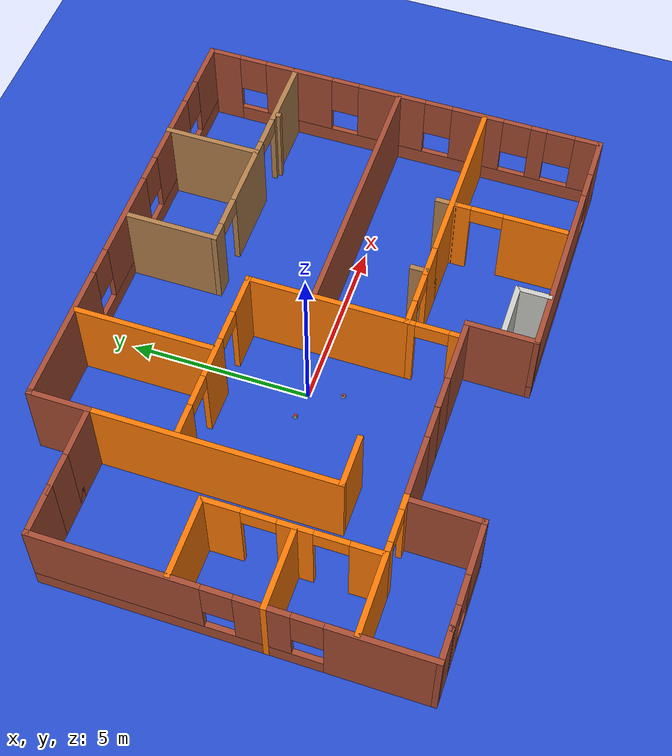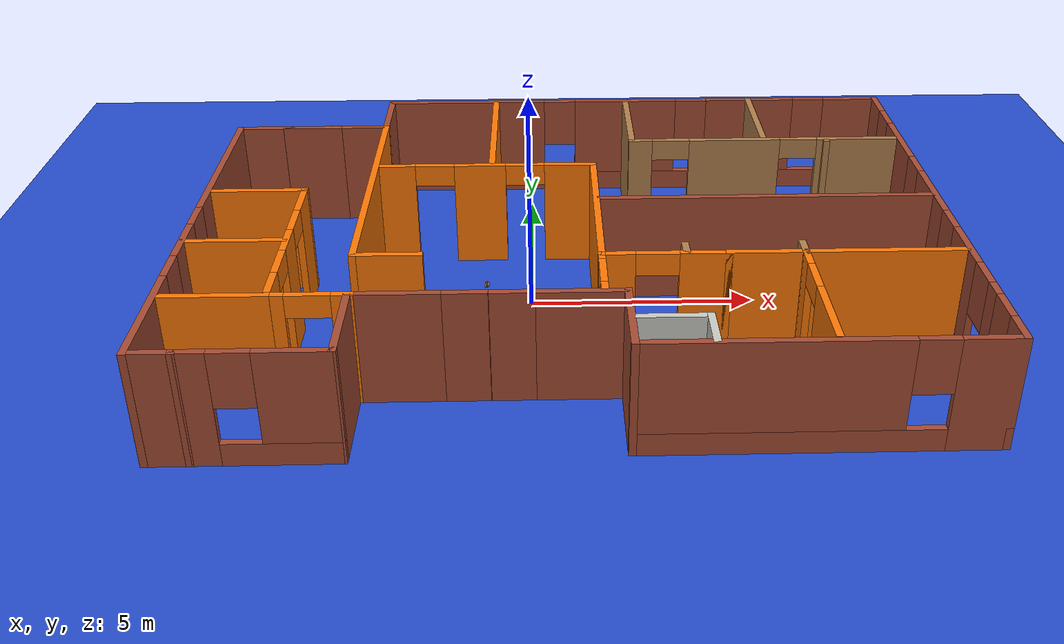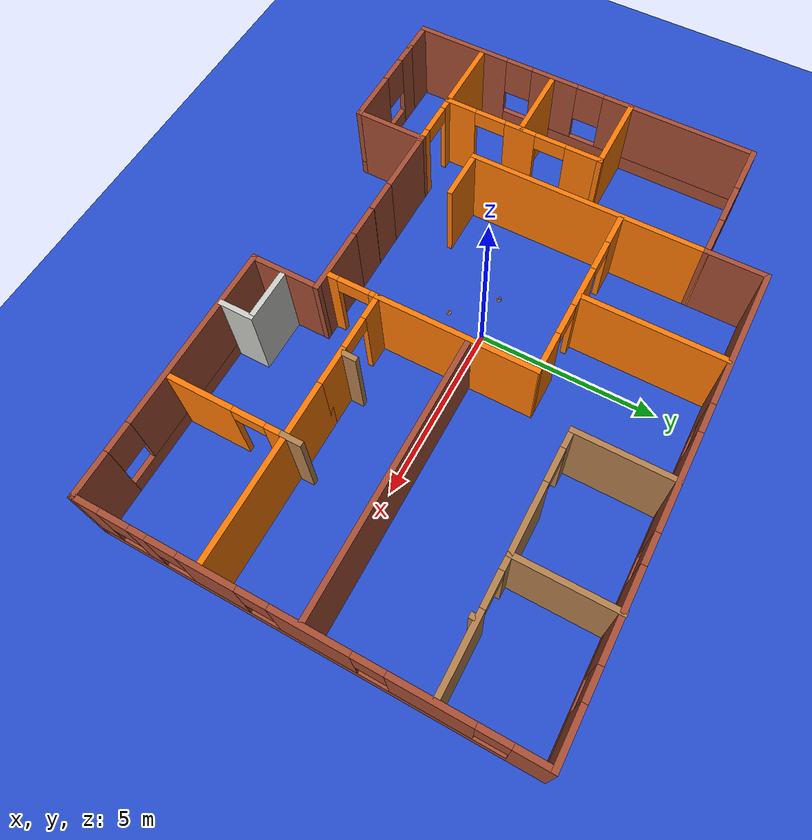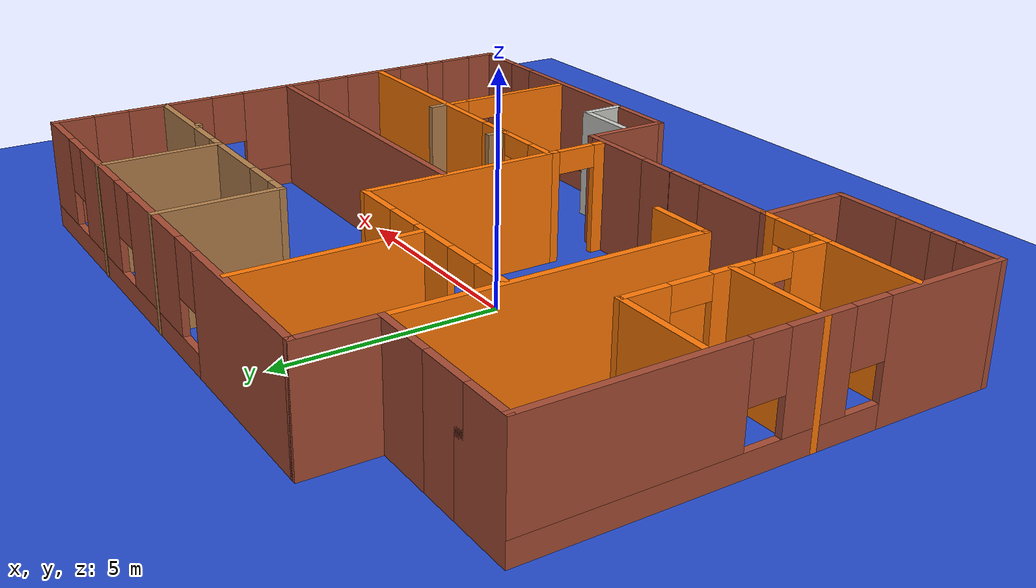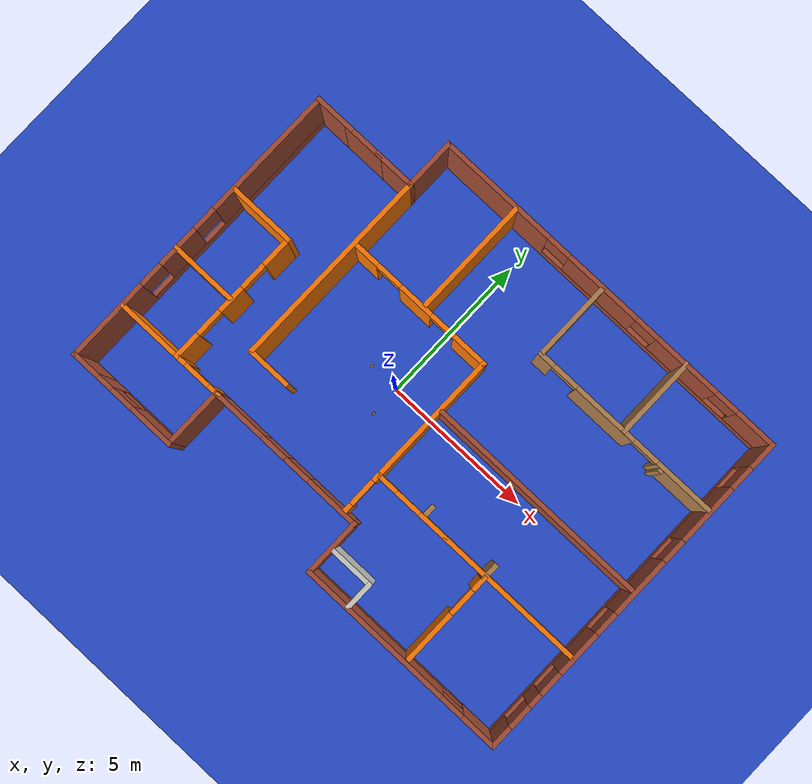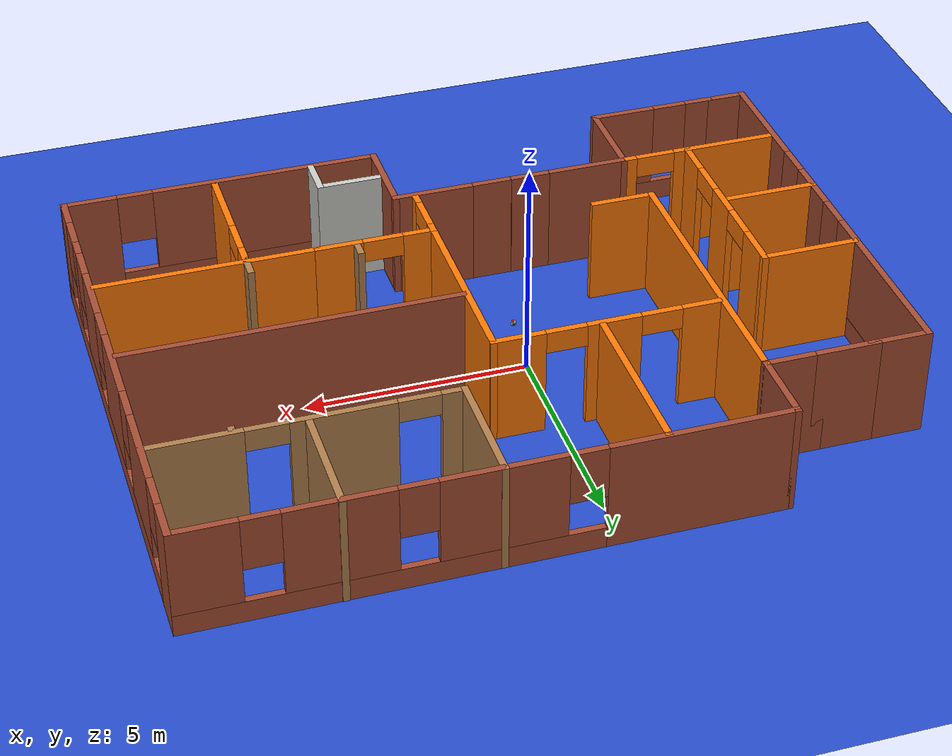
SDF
<sdf version="1.9">
 <world name="diff_drive">
  <physics name="default_physics" default="false" type="ode">
   <max_step_size>0.001</max_step_size>
   <real_time_factor>1</real_time_factor>
   <real_time_update_rate>1000</real_time_update_rate>
  </physics>
  <plugin name="ignition::gazebo::systems::Physics" filename="ignition-gazebo-physics-system"/>
  <plugin name="ignition::gazebo::systems::SceneBroadcaster" filename="ignition-gazebo-scene-broadcaster-system"/>
  <plugin name="gz::sim::systems::Sensors" filename="ignition-gazebo-sensors-system">
   <render_engine>ogre1</render_engine>
  </plugin>
  <gravity>0 0 -9.8</gravity>
  <magnetic_field>6e-06 2.3e-05 -4.2e-05</magnetic_field>
  <atmosphere type="adiabatic"/>
  <scene><ambient>0.4 0.4 0.4 1</ambient><background>0.7 0.7 0.7 1</background><shadows>true</shadows></scene>
  <model name="office">
   <pose>0.904802 0.213699 0 0 -0 0</pose>
   <link name="Wall_10">
    <collision name="Wall_10_Collision">
     <geometry><box><size>1 0.15 2.5</size></box></geometry>
     <pose>0 0 1.25 0 -0 0</pose>
    </collision>
    <visual name="Wall_10_Visual">
     <pose>0 0 1.25 0 -0 0</pose>
     <geometry><box><size>1 0.15 2.5</size></box></geometry>
     <material>
      <script><uri>file://media/materials/scripts/gazebo.material</uri><name>Gazebo/Bricks</name></script>
      <ambient>1 1 1 1</ambient>
     </material>
     <meta><layer>0</layer></meta>
    </visual>
    <pose>-7.67457 -5.85749 0 0 -0 3.14159</pose>
   </link>
   <link name="Wall_11">
    <pose>-8.09957 -0.807493 0 0 -0 1.5708</pose>
    <visual name="Wall_11_Visual_0">
     <pose>-3.7208 0 1.25 0 -0 0</pose>
     <geometry><box><size>2.8084 0.15 2.5</size></box></geometry>
     <material>
      <script><uri>file://media/materials/scripts/gazebo.material</uri><name>Gazebo/Bricks</name></script>
      <ambient>1 1 1 1</ambient>
     </material>
     <meta><layer>0</layer></meta>
    </visual>
    <collision name="Wall_11_Collision_0">
     <geometry><box><size>2.8084 0.15 2.5</size></box></geometry>
     <pose>-3.7208 0 1.25 0 -0 0</pose>
    </collision>
    <visual name="Wall_11_Visual_1">
     <pose>1.4042 0 0.25 0 -0 0</pose>
     <geometry><box><size>7.4416 0.15 0.5</size></box></geometry>
     <material>
      <script><uri>file://media/materials/scripts/gazebo.material</uri><name>Gazebo/Bricks</name></script>
      <ambient>1 1 1 1</ambient>
     </material>
     <meta><layer>0</layer></meta>
    </visual>
    <collision name="Wall_11_Collision_1">
     <geometry><box><size>7.4416 0.15 0.5</size></box></geometry>
     <pose>1.4042 0 0.25 0 -0 0</pose>
    </collision>
    <visual name="Wall_11_Visual_2">
     <pose>-0.81473 0 1.5 0 -0 0</pose>
     <geometry><box><size>1.40375 0.15 2</size></box></geometry>
     <material>
      <script><uri>file://media/materials/scripts/gazebo.material</uri><name>Gazebo/Bricks</name></script>
      <ambient>1 1 1 1</ambient>
     </material>
     <meta><layer>0</layer></meta>
    </visual>
    <collision name="Wall_11_Collision_2">
     <geometry><box><size>1.40375 0.15 2</size></box></geometry>
     <pose>-0.81473 0 1.5 0 -0 0</pose>
    </collision>
    <visual name="Wall_11_Visual_3">
     <pose>2.90607 0 1.5 0 -0 0</pose>
     <geometry><box><size>4.43786 0.15 2</size></box></geometry>
     <material>
      <script><uri>file://media/materials/scripts/gazebo.material</uri><name>Gazebo/Bricks</name></script>
      <ambient>1 1 1 1</ambient>
     </material>
     <meta><layer>0</layer></meta>
    </visual>
    <collision name="Wall_11_Collision_3">
     <geometry><box><size>4.43786 0.15 2</size></box></geometry>
     <pose>2.90607 0 1.5 0 -0 0</pose>
    </collision>
    <visual name="Wall_11_Visual_4">
     <pose>-1.9166 0 1.9 0 -0 0</pose>
     <geometry><box><size>0.8 0.15 1.2</size></box></geometry>
     <material>
      <script><uri>file://media/materials/scripts/gazebo.material</uri><name>Gazebo/Bricks</name></script>
      <ambient>1 1 1 1</ambient>
     </material>
     <meta><layer>0</layer></meta>
    </visual>
    <collision name="Wall_11_Collision_4">
     <geometry><box><size>0.8 0.15 1.2</size></box></geometry>
     <pose>-1.9166 0 1.9 0 -0 0</pose>
    </collision>
    <visual name="Wall_11_Visual_5">
     <pose>0.287144 0 1.9 0 -0 0</pose>
     <geometry><box><size>0.8 0.15 1.2</size></box></geometry>
     <material>
      <script><uri>file://media/materials/scripts/gazebo.material</uri><name>Gazebo/Bricks</name></script>
      <ambient>1 1 1 1</ambient>
     </material>
     <meta><layer>0</layer></meta>
    </visual>
    <collision name="Wall_11_Collision_5">
     <geometry><box><size>0.8 0.15 1.2</size></box></geometry>
     <pose>0.287144 0 1.9 0 -0 0</pose>
    </collision>
   </link>
   <link name="Wall_12">
    <pose>-6.29957 4.24251 0 0 -0 0</pose>
    <visual name="Wall_12_Visual_0">
     <pose>-1.17034 0 1.25 0 -0 0</pose>
     <geometry><box><size>1.40932 0.15 2.5</size></box></geometry>
     <material>
      <script><uri>file://media/materials/scripts/gazebo.material</uri><name>Gazebo/Bricks</name></script>
      <ambient>1 1 1 1</ambient>
     </material>
     <meta><layer>0</layer></meta>
    </visual>
    <collision name="Wall_12_Collision_0">
     <geometry><box><size>1.40932 0.15 2.5</size></box></geometry>
     <pose>-1.17034 0 1.25 0 -0 0</pose>
    </collision>
    <visual name="Wall_12_Visual_1">
     <pose>1.15466 0 1.25 0 -0 0</pose>
     <geometry><box><size>1.44068 0.15 2.5</size></box></geometry>
     <material>
      <script><uri>file://media/materials/scripts/gazebo.material</uri><name>Gazebo/Bricks</name></script>
      <ambient>1 1 1 1</ambient>
     </material>
     <meta><layer>0</layer></meta>
    </visual>
    <collision name="Wall_12_Collision_1">
     <geometry><box><size>1.44068 0.15 2.5</size></box></geometry>
     <pose>1.15466 0 1.25 0 -0 0</pose>
    </collision>
    <visual name="Wall_12_Visual_2">
     <pose>-0.015683 0 1.25 0 -0 0</pose>
     <geometry><box><size>1.44068 0.15 2.5</size></box></geometry>
     <material>
      <script><uri>file://media/materials/scripts/gazebo.material</uri><name>Gazebo/Bricks</name></script>
      <ambient>1 1 1 1</ambient>
     </material>
     <meta><layer>0</layer></meta>
    </visual>
    <collision name="Wall_12_Collision_2">
     <geometry><box><size>1.44068 0.15 2.5</size></box></geometry>
     <pose>-0.015683 0 1.25 0 -0 0</pose>
    </collision>
   </link>
   <link name="Wall_13">
    <collision name="Wall_13_Collision">
     <geometry><box><size>1.75 0.15 2.5</size></box></geometry>
     <pose>0 0 1.25 0 -0 0</pose>
    </collision>
    <visual name="Wall_13_Visual">
     <pose>0 0 1.25 0 -0 0</pose>
     <geometry><box><size>1.75 0.15 2.5</size></box></geometry>
     <material>
      <script><uri>file://media/materials/scripts/gazebo.material</uri><name>Gazebo/Bricks</name></script>
      <ambient>1 1 1 1</ambient>
     </material>
     <meta><layer>0</layer></meta>
    </visual>
    <pose>-4.49957 5.04251 0 0 -0 1.5708</pose>
   </link>
   <link name="Wall_14">
    <pose>1.80043 5.84251 0 0 -0 0</pose>
    <visual name="Wall_14_Visual_0">
     <pose>-4.36709 0 1.25 0 -0 0</pose>
     <geometry><box><size>4.01582 0.15 2.5</size></box></geometry>
     <material>
      <script><uri>file://media/materials/scripts/gazebo.material</uri><name>Gazebo/Bricks</name></script>
      <ambient>1 1 1 1</ambient>
     </material>
     <meta><layer>0</layer></meta>
    </visual>
    <collision name="Wall_14_Collision_0">
     <geometry><box><size>4.01582 0.15 2.5</size></box></geometry>
     <pose>-4.36709 0 1.25 0 -0 0</pose>
    </collision>
    <visual name="Wall_14_Visual_1">
     <pose>2.00791 0 0.25 0 -0 0</pose>
     <geometry><box><size>8.73418 0.15 0.5</size></box></geometry>
     <material>
      <script><uri>file://media/materials/scripts/gazebo.material</uri><name>Gazebo/Bricks</name></script>
      <ambient>1 1 1 1</ambient>
     </material>
     <meta><layer>0</layer></meta>
    </visual>
    <collision name="Wall_14_Collision_1">
     <geometry><box><size>8.73418 0.15 0.5</size></box></geometry>
     <pose>2.00791 0 0.25 0 -0 0</pose>
    </collision>
    <visual name="Wall_14_Visual_2">
     <pose>-0.245155 0 1.5 0 -0 0</pose>
     <geometry><box><size>2.62805 0.15 2</size></box></geometry>
     <material>
      <script><uri>file://media/materials/scripts/gazebo.material</uri><name>Gazebo/Bricks</name></script>
      <ambient>1 1 1 1</ambient>
     </material>
     <meta><layer>0</layer></meta>
    </visual>
    <collision name="Wall_14_Collision_2">
     <geometry><box><size>2.62805 0.15 2</size></box></geometry>
     <pose>-0.245155 0 1.5 0 -0 0</pose>
    </collision>
    <visual name="Wall_14_Visual_3">
     <pose>3.008 0 1.5 0 -0 0</pose>
     <geometry><box><size>2.27825 0.15 2</size></box></geometry>
     <material>
      <script><uri>file://media/materials/scripts/gazebo.material</uri><name>Gazebo/Bricks</name></script>
      <ambient>1 1 1 1</ambient>
     </material>
     <meta><layer>0</layer></meta>
    </visual>
    <collision name="Wall_14_Collision_3">
     <geometry><box><size>2.27825 0.15 2</size></box></geometry>
     <pose>3.008 0 1.5 0 -0 0</pose>
    </collision>
    <visual name="Wall_14_Visual_4">
     <pose>5.66106 0 1.5 0 -0 0</pose>
     <geometry><box><size>1.42788 0.15 2</size></box></geometry>
     <material>
      <script><uri>file://media/materials/scripts/gazebo.material</uri><name>Gazebo/Bricks</name></script>
      <ambient>1 1 1 1</ambient>
     </material>
     <meta><layer>0</layer></meta>
    </visual>
    <collision name="Wall_14_Collision_4">
     <geometry><box><size>1.42788 0.15 2</size></box></geometry>
     <pose>5.66106 0 1.5 0 -0 0</pose>
    </collision>
    <visual name="Wall_14_Visual_5">
     <pose>-1.95918 0 1.9 0 -0 0</pose>
     <geometry><box><size>0.8 0.15 1.2</size></box></geometry>
     <material>
      <script><uri>file://media/materials/scripts/gazebo.material</uri><name>Gazebo/Bricks</name></script>
      <ambient>1 1 1 1</ambient>
     </material>
     <meta><layer>0</layer></meta>
    </visual>
    <collision name="Wall_14_Collision_5">
     <geometry><box><size>0.8 0.15 1.2</size></box></geometry>
     <pose>-1.95918 0 1.9 0 -0 0</pose>
    </collision>
    <visual name="Wall_14_Visual_6">
     <pose>1.46887 0 1.9 0 -0 0</pose>
     <geometry><box><size>0.8 0.15 1.2</size></box></geometry>
     <material>
      <script><uri>file://media/materials/scripts/gazebo.material</uri><name>Gazebo/Bricks</name></script>
      <ambient>1 1 1 1</ambient>
     </material>
     <meta><layer>0</layer></meta>
    </visual>
    <collision name="Wall_14_Collision_6">
     <geometry><box><size>0.8 0.15 1.2</size></box></geometry>
     <pose>1.46887 0 1.9 0 -0 0</pose>
    </collision>
    <visual name="Wall_14_Visual_7">
     <pose>4.54712 0 1.9 0 -0 0</pose>
     <geometry><box><size>0.8 0.15 1.2</size></box></geometry>
     <material>
      <script><uri>file://media/materials/scripts/gazebo.material</uri><name>Gazebo/Bricks</name></script>
      <ambient>1 1 1 1</ambient>
     </material>
     <meta><layer>0</layer></meta>
    </visual>
    <collision name="Wall_14_Collision_7">
     <geometry><box><size>0.8 0.15 1.2</size></box></geometry>
     <pose>4.54712 0 1.9 0 -0 0</pose>
    </collision>
   </link>
   <link name="Wall_15">
    <pose>8.10043 0.042507 0 0 0 -1.5708</pose>
    <visual name="Wall_15_Visual_0">
     <pose>-5.39213 0 1.25 0 -0 0</pose>
     <geometry><box><size>0.965738 0.15 2.5</size></box></geometry>
     <material>
      <script><uri>file://media/materials/scripts/gazebo.material</uri><name>Gazebo/Bricks</name></script>
      <ambient>1 1 1 1</ambient>
     </material>
     <meta><layer>0</layer></meta>
    </visual>
    <collision name="Wall_15_Collision_0">
     <geometry><box><size>0.965738 0.15 2.5</size></box></geometry>
     <pose>-5.39213 0 1.25 0 -0 0</pose>
    </collision>
    <visual name="Wall_15_Visual_1">
     <pose>0.482869 0 0.25 0 -0 0</pose>
     <geometry><box><size>10.7843 0.15 0.5</size></box></geometry>
     <material>
      <script><uri>file://media/materials/scripts/gazebo.material</uri><name>Gazebo/Bricks</name></script>
      <ambient>1 1 1 1</ambient>
     </material>
     <meta><layer>0</layer></meta>
    </visual>
    <collision name="Wall_15_Collision_1">
     <geometry><box><size>10.7843 0.15 0.5</size></box></geometry>
     <pose>0.482869 0 0.25 0 -0 0</pose>
    </collision>
    <visual name="Wall_15_Visual_2">
     <pose>-3.09257 0 1.5 0 -0 0</pose>
     <geometry><box><size>2.03339 0.15 2</size></box></geometry>
     <material>
      <script><uri>file://media/materials/scripts/gazebo.material</uri><name>Gazebo/Bricks</name></script>
      <ambient>1 1 1 1</ambient>
     </material>
     <meta><layer>0</layer></meta>
    </visual>
    <collision name="Wall_15_Collision_2">
     <geometry><box><size>2.03339 0.15 2</size></box></geometry>
     <pose>-3.09257 0 1.5 0 -0 0</pose>
    </collision>
    <visual name="Wall_15_Visual_3">
     <pose>-0.276667 0 1.5 0 -0 0</pose>
     <geometry><box><size>1.99841 0.15 2</size></box></geometry>
     <material>
      <script><uri>file://media/materials/scripts/gazebo.material</uri><name>Gazebo/Bricks</name></script>
      <ambient>1 1 1 1</ambient>
     </material>
     <meta><layer>0</layer></meta>
    </visual>
    <collision name="Wall_15_Collision_3">
     <geometry><box><size>1.99841 0.15 2</size></box></geometry>
     <pose>-0.276667 0 1.5 0 -0 0</pose>
    </collision>
    <visual name="Wall_15_Visual_4">
     <pose>2.27688 0 1.5 0 -0 0</pose>
     <geometry><box><size>1.50869 0.15 2</size></box></geometry>
     <material>
      <script><uri>file://media/materials/scripts/gazebo.material</uri><name>Gazebo/Bricks</name></script>
      <ambient>1 1 1 1</ambient>
     </material>
     <meta><layer>0</layer></meta>
    </visual>
    <collision name="Wall_15_Collision_4">
     <geometry><box><size>1.50869 0.15 2</size></box></geometry>
     <pose>2.27688 0 1.5 0 -0 0</pose>
    </collision>
    <visual name="Wall_15_Visual_5">
     <pose>4.06087 0 1.5 0 -0 0</pose>
     <geometry><box><size>0.459284 0.15 2</size></box></geometry>
     <material>
      <script><uri>file://media/materials/scripts/gazebo.material</uri><name>Gazebo/Bricks</name></script>
      <ambient>1 1 1 1</ambient>
     </material>
     <meta><layer>0</layer></meta>
    </visual>
    <collision name="Wall_15_Collision_5">
     <geometry><box><size>0.459284 0.15 2</size></box></geometry>
     <pose>4.06087 0 1.5 0 -0 0</pose>
    </collision>
    <visual name="Wall_15_Visual_6">
     <pose>5.48276 0 1.5 0 -0 0</pose>
     <geometry><box><size>0.784489 0.15 2</size></box></geometry>
     <material>
      <script><uri>file://media/materials/scripts/gazebo.material</uri><name>Gazebo/Bricks</name></script>
      <ambient>1 1 1 1</ambient>
     </material>
     <meta><layer>0</layer></meta>
    </visual>
    <collision name="Wall_15_Collision_6">
     <geometry><box><size>0.784489 0.15 2</size></box></geometry>
     <pose>5.48276 0 1.5 0 -0 0</pose>
    </collision>
    <visual name="Wall_15_Visual_7">
     <pose>-4.50926 0 1.9 0 -0 0</pose>
     <geometry><box><size>0.8 0.15 1.2</size></box></geometry>
     <material>
      <script><uri>file://media/materials/scripts/gazebo.material</uri><name>Gazebo/Bricks</name></script>
      <ambient>1 1 1 1</ambient>
     </material>
     <meta><layer>0</layer></meta>
    </visual>
    <collision name="Wall_15_Collision_7">
     <geometry><box><size>0.8 0.15 1.2</size></box></geometry>
     <pose>-4.50926 0 1.9 0 -0 0</pose>
    </collision>
    <visual name="Wall_15_Visual_8">
     <pose>-1.67587 0 1.9 0 -0 0</pose>
     <geometry><box><size>0.8 0.15 1.2</size></box></geometry>
     <material>
      <script><uri>file://media/materials/scripts/gazebo.material</uri><name>Gazebo/Bricks</name></script>
      <ambient>1 1 1 1</ambient>
     </material>
     <meta><layer>0</layer></meta>
    </visual>
    <collision name="Wall_15_Collision_8">
     <geometry><box><size>0.8 0.15 1.2</size></box></geometry>
     <pose>-1.67587 0 1.9 0 -0 0</pose>
    </collision>
    <visual name="Wall_15_Visual_9">
     <pose>1.12254 0 1.9 0 -0 0</pose>
     <geometry><box><size>0.8 0.15 1.2</size></box></geometry>
     <material>
      <script><uri>file://media/materials/scripts/gazebo.material</uri><name>Gazebo/Bricks</name></script>
      <ambient>1 1 1 1</ambient>
     </material>
     <meta><layer>0</layer></meta>
    </visual>
    <collision name="Wall_15_Collision_9">
     <geometry><box><size>0.8 0.15 1.2</size></box></geometry>
     <pose>1.12254 0 1.9 0 -0 0</pose>
    </collision>
    <visual name="Wall_15_Visual_10">
     <pose>3.43123 0 1.9 0 -0 0</pose>
     <geometry><box><size>0.8 0.15 1.2</size></box></geometry>
     <material>
      <script><uri>file://media/materials/scripts/gazebo.material</uri><name>Gazebo/Bricks</name></script>
      <ambient>1 1 1 1</ambient>
     </material>
     <meta><layer>0</layer></meta>
    </visual>
    <collision name="Wall_15_Collision_10">
     <geometry><box><size>0.8 0.15 1.2</size></box></geometry>
     <pose>3.43123 0 1.9 0 -0 0</pose>
    </collision>
    <visual name="Wall_15_Visual_11">
     <pose>4.69051 0 1.9 0 -0 0</pose>
     <geometry><box><size>0.8 0.15 1.2</size></box></geometry>
     <material>
      <script><uri>file://media/materials/scripts/gazebo.material</uri><name>Gazebo/Bricks</name></script>
      <ambient>1 1 1 1</ambient>
     </material>
     <meta><layer>0</layer></meta>
    </visual>
    <collision name="Wall_15_Collision_11">
     <geometry><box><size>0.8 0.15 1.2</size></box></geometry>
     <pose>4.69051 0 1.9 0 -0 0</pose>
    </collision>
   </link>
   <link name="Wall_21">
    <pose>4.55043 -5.75749 0 0 -0 3.14159</pose>
    <visual name="Wall_21_Visual_0">
     <pose>-2.99851 0 1.25 0 -0 0</pose>
     <geometry><box><size>1.25298 0.15 2.5</size></box></geometry>
     <material>
      <script><uri>file://media/materials/scripts/gazebo.material</uri><name>Gazebo/Bricks</name></script>
      <ambient>1 1 1 1</ambient>
     </material>
     <meta><layer>0</layer></meta>
    </visual>
    <collision name="Wall_21_Collision_0">
     <geometry><box><size>1.25298 0.15 2.5</size></box></geometry>
     <pose>-2.99851 0 1.25 0 -0 0</pose>
    </collision>
    <visual name="Wall_21_Visual_1">
     <pose>0.626488 0 0.25 0 -0 0</pose>
     <geometry><box><size>5.99702 0.15 0.5</size></box></geometry>
     <material>
      <script><uri>file://media/materials/scripts/gazebo.material</uri><name>Gazebo/Bricks</name></script>
      <ambient>1 1 1 1</ambient>
     </material>
     <meta><layer>0</layer></meta>
    </visual>
    <collision name="Wall_21_Collision_1">
     <geometry><box><size>5.99702 0.15 0.5</size></box></geometry>
     <pose>0.626488 0 0.25 0 -0 0</pose>
    </collision>
    <visual name="Wall_21_Visual_2">
     <pose>1.02649 0 1.5 0 -0 0</pose>
     <geometry><box><size>5.19702 0.15 2</size></box></geometry>
     <material>
      <script><uri>file://media/materials/scripts/gazebo.material</uri><name>Gazebo/Bricks</name></script>
      <ambient>1 1 1 1</ambient>
     </material>
     <meta><layer>0</layer></meta>
    </visual>
    <collision name="Wall_21_Collision_2">
     <geometry><box><size>5.19702 0.15 2</size></box></geometry>
     <pose>1.02649 0 1.5 0 -0 0</pose>
    </collision>
    <visual name="Wall_21_Visual_3">
     <pose>-1.97202 0 1.9 0 -0 0</pose>
     <geometry><box><size>0.8 0.15 1.2</size></box></geometry>
     <material>
      <script><uri>file://media/materials/scripts/gazebo.material</uri><name>Gazebo/Bricks</name></script>
      <ambient>1 1 1 1</ambient>
     </material>
     <meta><layer>0</layer></meta>
    </visual>
    <collision name="Wall_21_Collision_3">
     <geometry><box><size>0.8 0.15 1.2</size></box></geometry>
     <pose>-1.97202 0 1.9 0 -0 0</pose>
    </collision>
   </link>
   <link name="Wall_22">
    <collision name="Wall_22_Collision">
     <geometry><box><size>2 0.15 2.5</size></box></geometry>
     <pose>0 0 1.25 0 -0 0</pose>
    </collision>
    <visual name="Wall_22_Visual">
     <pose>0 0 1.25 0 -0 0</pose>
     <geometry><box><size>2 0.15 2.5</size></box></geometry>
     <material>
      <script><uri>file://media/materials/scripts/gazebo.material</uri><name>Gazebo/Bricks</name></script>
      <ambient>1 1 1 1</ambient>
     </material>
     <meta><layer>0</layer></meta>
    </visual>
    <pose>1.00043 -4.83249 0 0 -0 1.5708</pose>
   </link>
   <link name="Wall_23">
    <pose>-1.67457 -3.90749 0 0 -0 3.14159</pose>
    <visual name="Wall_23_Visual_0">
     <pose>-1.81572 0 1.25 0 -0 0</pose>
     <geometry><box><size>1.86857 0.15 2.5</size></box></geometry>
     <material>
      <script><uri>file://media/materials/scripts/gazebo.material</uri><name>Gazebo/Bricks</name></script>
      <ambient>1 1 1 1</ambient>
     </material>
     <meta><layer>0</layer></meta>
    </visual>
    <collision name="Wall_23_Collision_0">
     <geometry><box><size>1.86857 0.15 2.5</size></box></geometry>
     <pose>-1.81572 0 1.25 0 -0 0</pose>
    </collision>
    <visual name="Wall_23_Visual_1">
     <pose>0.023306 0 1.25 0 -0 0</pose>
     <geometry><box><size>0.009483 0.15 2.5</size></box></geometry>
     <material>
      <script><uri>file://media/materials/scripts/gazebo.material</uri><name>Gazebo/Bricks</name></script>
      <ambient>1 1 1 1</ambient>
     </material>
     <meta><layer>0</layer></meta>
    </visual>
    <collision name="Wall_23_Collision_1">
     <geometry><box><size>0.009483 0.15 2.5</size></box></geometry>
     <pose>0.023306 0 1.25 0 -0 0</pose>
    </collision>
    <visual name="Wall_23_Visual_2">
     <pose>1.83902 0 1.25 0 -0 0</pose>
     <geometry><box><size>1.82195 0.15 2.5</size></box></geometry>
     <material>
      <script><uri>file://media/materials/scripts/gazebo.material</uri><name>Gazebo/Bricks</name></script>
      <ambient>1 1 1 1</ambient>
     </material>
     <meta><layer>0</layer></meta>
    </visual>
    <collision name="Wall_23_Collision_2">
     <geometry><box><size>1.82195 0.15 2.5</size></box></geometry>
     <pose>1.83902 0 1.25 0 -0 0</pose>
    </collision>
    <visual name="Wall_23_Visual_3">
     <pose>-0.431435 0 1.25 0 -0 0</pose>
     <geometry><box><size>0.9 0.15 2.5</size></box></geometry>
     <material>
      <script><uri>file://media/materials/scripts/gazebo.material</uri><name>Gazebo/Bricks</name></script>
      <ambient>1 1 1 1</ambient>
     </material>
     <meta><layer>0</layer></meta>
    </visual>
    <collision name="Wall_23_Collision_3">
     <geometry><box><size>0.9 0.15 2.5</size></box></geometry>
     <pose>-0.431435 0 1.25 0 -0 0</pose>
    </collision>
    <visual name="Wall_23_Visual_4">
     <pose>0.478048 0 1.25 0 -0 0</pose>
     <geometry><box><size>0.9 0.15 2.5</size></box></geometry>
     <material>
      <script><uri>file://media/materials/scripts/gazebo.material</uri><name>Gazebo/Bricks</name></script>
      <ambient>1 1 1 1</ambient>
     </material>
     <meta><layer>0</layer></meta>
    </visual>
    <collision name="Wall_23_Collision_4">
     <geometry><box><size>0.9 0.15 2.5</size></box></geometry>
     <pose>0.478048 0 1.25 0 -0 0</pose>
    </collision>
   </link>
   <link name="Wall_25">
    <pose>-5.14957 -3.90749 0 0 -0 3.14159</pose>
    <visual name="Wall_25_Visual_0">
     <pose>-0.656831 0 1.25 0 -0 0</pose>
     <geometry><box><size>0.436339 0.15 2.5</size></box></geometry>
     <material>
      <script><uri>file://media/materials/scripts/gazebo.material</uri><name>Gazebo/Grey</name></script>
      <ambient>0.996078 0.47451 0.0196078 1</ambient>
     </material>
     <meta><layer>0</layer></meta>
    </visual>
    <collision name="Wall_25_Collision_0">
     <geometry><box><size>0.436339 0.15 2.5</size></box></geometry>
     <pose>-0.656831 0 1.25 0 -0 0</pose>
    </collision>
    <visual name="Wall_25_Visual_1">
     <pose>0.668169 0 1.25 0 -0 0</pose>
     <geometry><box><size>0.413661 0.15 2.5</size></box></geometry>
     <material>
      <script><uri>file://media/materials/scripts/gazebo.material</uri><name>Gazebo/Grey</name></script>
      <ambient>0.996078 0.47451 0.0196078 1</ambient>
     </material>
     <meta><layer>0</layer></meta>
    </visual>
    <collision name="Wall_25_Collision_1">
     <geometry><box><size>0.413661 0.15 2.5</size></box></geometry>
     <pose>0.668169 0 1.25 0 -0 0</pose>
    </collision>
    <visual name="Wall_25_Visual_2">
     <pose>0.011339 0 2.25 0 -0 0</pose>
     <geometry><box><size>0.9 0.15 0.5</size></box></geometry>
     <material>
      <script><uri>file://media/materials/scripts/gazebo.material</uri><name>Gazebo/Grey</name></script>
      <ambient>0.996078 0.47451 0.0196078 1</ambient>
     </material>
     <meta><layer>0</layer></meta>
    </visual>
    <collision name="Wall_25_Collision_2">
     <geometry><box><size>0.9 0.15 0.5</size></box></geometry>
     <pose>0.011339 0 2.25 0 -0 0</pose>
    </collision>
   </link>
   <link name="Wall_26">
    <pose>-5.94957 -1.60749 0 0 -0 1.5708</pose>
    <visual name="Wall_26_Visual_0">
     <pose>-1.90084 0 1.25 0 -0 0</pose>
     <geometry><box><size>0.948317 0.15 2.5</size></box></geometry>
     <material>
      <script><uri>file://media/materials/scripts/gazebo.material</uri><name>Gazebo/Grey</name></script>
      <ambient>0.996078 0.47451 0.0196078 1</ambient>
     </material>
     <meta><layer>0</layer></meta>
    </visual>
    <collision name="Wall_26_Collision_0">
     <geometry><box><size>0.948317 0.15 2.5</size></box></geometry>
     <pose>-1.90084 0 1.25 0 -0 0</pose>
    </collision>
    <visual name="Wall_26_Visual_1">
     <pose>-0.0672 0 1.25 0 -0 0</pose>
     <geometry><box><size>0.918967 0.15 2.5</size></box></geometry>
     <material>
      <script><uri>file://media/materials/scripts/gazebo.material</uri><name>Gazebo/Grey</name></script>
      <ambient>0.996078 0.47451 0.0196078 1</ambient>
     </material>
     <meta><layer>0</layer></meta>
    </visual>
    <collision name="Wall_26_Collision_1">
     <geometry><box><size>0.918967 0.15 2.5</size></box></geometry>
     <pose>-0.0672 0 1.25 0 -0 0</pose>
    </collision>
    <visual name="Wall_26_Visual_2">
     <pose>1.83364 0 1.25 0 -0 0</pose>
     <geometry><box><size>1.08272 0.15 2.5</size></box></geometry>
     <material>
      <script><uri>file://media/materials/scripts/gazebo.material</uri><name>Gazebo/Grey</name></script>
      <ambient>0.996078 0.47451 0.0196078 1</ambient>
     </material>
     <meta><layer>0</layer></meta>
    </visual>
    <collision name="Wall_26_Collision_2">
     <geometry><box><size>1.08272 0.15 2.5</size></box></geometry>
     <pose>1.83364 0 1.25 0 -0 0</pose>
    </collision>
    <visual name="Wall_26_Visual_3">
     <pose>-0.976683 0 2.25 0 -0 0</pose>
     <geometry><box><size>0.9 0.15 0.5</size></box></geometry>
     <material>
      <script><uri>file://media/materials/scripts/gazebo.material</uri><name>Gazebo/Grey</name></script>
      <ambient>0.996078 0.47451 0.0196078 1</ambient>
     </material>
     <meta><layer>0</layer></meta>
    </visual>
    <collision name="Wall_26_Collision_3">
     <geometry><box><size>0.9 0.15 0.5</size></box></geometry>
     <pose>-0.976683 0 2.25 0 -0 0</pose>
    </collision>
    <visual name="Wall_26_Visual_4">
     <pose>0.842283 0 2.25 0 -0 0</pose>
     <geometry><box><size>0.9 0.15 0.5</size></box></geometry>
     <material>
      <script><uri>file://media/materials/scripts/gazebo.material</uri><name>Gazebo/Grey</name></script>
      <ambient>0.996078 0.47451 0.0196078 1</ambient>
     </material>
     <meta><layer>0</layer></meta>
    </visual>
    <collision name="Wall_26_Collision_4">
     <geometry><box><size>0.9 0.15 0.5</size></box></geometry>
     <pose>0.842283 0 2.25 0 -0 0</pose>
    </collision>
   </link>
   <link name="Wall_29">
    <collision name="Wall_29_Collision">
     <geometry><box><size>2.25 0.15 2.5</size></box></geometry>
     <pose>0 0 1.25 0 -0 0</pose>
    </collision>
    <visual name="Wall_29_Visual">
     <pose>0 0 1.25 0 -0 0</pose>
     <geometry><box><size>2.25 0.15 2.5</size></box></geometry>
     <material>
      <script><uri>file://media/materials/scripts/gazebo.material</uri><name>Gazebo/Grey</name></script>
      <ambient>0.996078 0.47451 0.0196078 1</ambient>
     </material>
     <meta><layer>0</layer></meta>
    </visual>
    <pose>-6.99957 0.692507 0 0 -0 3.14159</pose>
   </link>
   <link name="Wall_31">
    <collision name="Wall_31_Collision">
     <geometry><box><size>6.75 0.15 2.5</size></box></geometry>
     <pose>0 0 1.25 0 -0 0</pose>
    </collision>
    <visual name="Wall_31_Visual">
     <pose>0 0 1.25 0 -0 0</pose>
     <geometry><box><size>6.75 0.15 2.5</size></box></geometry>
     <material>
      <script><uri>file://media/materials/scripts/gazebo.material</uri><name>Gazebo/Grey</name></script>
      <ambient>0.996078 0.47451 0.0196078 1</ambient>
     </material>
     <meta><layer>0</layer></meta>
    </visual>
    <pose>-4.49978 0.942713 0 0 0 -1.57086</pose>
   </link>
   <link name="Wall_32">
    <collision name="Wall_32_Collision">
     <geometry><box><size>1.5 0.15 2.5</size></box></geometry>
     <pose>0 0 1.25 0 -0 0</pose>
    </collision>
    <visual name="Wall_32_Visual">
     <pose>0 0 1.25 0 -0 0</pose>
     <geometry><box><size>1.5 0.15 2.5</size></box></geometry>
     <material>
      <script><uri>file://media/materials/scripts/gazebo.material</uri><name>Gazebo/Grey</name></script>
      <ambient>0.996078 0.47451 0.0196078 1</ambient>
     </material>
     <meta><layer>0</layer></meta>
    </visual>
    <pose>-3.82498 -2.35708 0 0 -0 0</pose>
   </link>
   <link name="Wall_34">
    <collision name="Wall_34_Collision">
     <geometry><box><size>4.5 0.15 2.5</size></box></geometry>
     <pose>0 0 1.25 0 -0 0</pose>
    </collision>
    <visual name="Wall_34_Visual">
     <pose>0 0 1.25 0 -0 0</pose>
     <geometry><box><size>4.5 0.15 2.5</size></box></geometry>
     <material>
      <script><uri>file://media/materials/scripts/gazebo.material</uri><name>Gazebo/Grey</name></script>
      <ambient>0.996078 0.47451 0.0196078 1</ambient>
     </material>
     <meta><layer>0</layer></meta>
    </visual>
    <pose>0.554111 -0.259019 0 0 -0 1.57084</pose>
   </link>
   <link name="Wall_37">
    <pose>-1.92098 1.91592 0 0 -0 3.14159</pose>
    <visual name="Wall_37_Visual_0">
     <pose>-1.94386 0 1.25 0 -0 0</pose>
     <geometry><box><size>1.21227 0.15 2.5</size></box></geometry>
     <material>
      <script><uri>file://media/materials/scripts/gazebo.material</uri><name>Gazebo/Grey</name></script>
      <ambient>0.996078 0.47451 0.0196078 1</ambient>
     </material>
     <meta><layer>0</layer></meta>
    </visual>
    <collision name="Wall_37_Collision_0">
     <geometry><box><size>1.21227 0.15 2.5</size></box></geometry>
     <pose>-1.94386 0 1.25 0 -0 0</pose>
    </collision>
    <visual name="Wall_37_Visual_1">
     <pose>0.161675 0 1.25 0 -0 0</pose>
     <geometry><box><size>1.19881 0.15 2.5</size></box></geometry>
     <material>
      <script><uri>file://media/materials/scripts/gazebo.material</uri><name>Gazebo/Grey</name></script>
      <ambient>0.996078 0.47451 0.0196078 1</ambient>
     </material>
     <meta><layer>0</layer></meta>
    </visual>
    <collision name="Wall_37_Collision_1">
     <geometry><box><size>1.19881 0.15 2.5</size></box></geometry>
     <pose>0.161675 0 1.25 0 -0 0</pose>
    </collision>
    <visual name="Wall_37_Visual_2">
     <pose>2.10554 0 1.25 0 -0 0</pose>
     <geometry><box><size>0.888921 0.15 2.5</size></box></geometry>
     <material>
      <script><uri>file://media/materials/scripts/gazebo.material</uri><name>Gazebo/Grey</name></script>
      <ambient>0.996078 0.47451 0.0196078 1</ambient>
     </material>
     <meta><layer>0</layer></meta>
    </visual>
    <collision name="Wall_37_Collision_2">
     <geometry><box><size>0.888921 0.15 2.5</size></box></geometry>
     <pose>2.10554 0 1.25 0 -0 0</pose>
    </collision>
    <visual name="Wall_37_Visual_3">
     <pose>-0.887729 0 2.25 0 -0 0</pose>
     <geometry><box><size>0.9 0.15 0.5</size></box></geometry>
     <material>
      <script><uri>file://media/materials/scripts/gazebo.material</uri><name>Gazebo/Grey</name></script>
      <ambient>0.996078 0.47451 0.0196078 1</ambient>
     </material>
     <meta><layer>0</layer></meta>
    </visual>
    <collision name="Wall_37_Collision_3">
     <geometry><box><size>0.9 0.15 0.5</size></box></geometry>
     <pose>-0.887729 0 2.25 0 -0 0</pose>
    </collision>
    <visual name="Wall_37_Visual_4">
     <pose>1.21108 0 2.25 0 -0 0</pose>
     <geometry><box><size>0.9 0.15 0.5</size></box></geometry>
     <material>
      <script><uri>file://media/materials/scripts/gazebo.material</uri><name>Gazebo/Grey</name></script>
      <ambient>0.996078 0.47451 0.0196078 1</ambient>
     </material>
     <meta><layer>0</layer></meta>
    </visual>
    <collision name="Wall_37_Collision_4">
     <geometry><box><size>0.9 0.15 0.5</size></box></geometry>
     <pose>1.21108 0 2.25 0 -0 0</pose>
    </collision>
   </link>
   <link name="Wall_39">
    <pose>1.85421 -2.43396 0 0 -0 0</pose>
    <visual name="Wall_39_Visual_0">
     <pose>-0.992004 0 1.25 0 -0 0</pose>
     <geometry><box><size>0.765991 0.15 2.5</size></box></geometry>
     <material>
      <script><uri>file://media/materials/scripts/gazebo.material</uri><name>Gazebo/Grey</name></script>
      <ambient>0.996078 0.47451 0.0196078 1</ambient>
     </material>
     <meta><layer>0</layer></meta>
    </visual>
    <collision name="Wall_39_Collision_0">
     <geometry><box><size>0.765991 0.15 2.5</size></box></geometry>
     <pose>-0.992004 0 1.25 0 -0 0</pose>
    </collision>
    <visual name="Wall_39_Visual_1">
     <pose>0.832996 0 1.25 0 -0 0</pose>
     <geometry><box><size>1.08401 0.15 2.5</size></box></geometry>
     <material>
      <script><uri>file://media/materials/scripts/gazebo.material</uri><name>Gazebo/Grey</name></script>
      <ambient>0.996078 0.47451 0.0196078 1</ambient>
     </material>
     <meta><layer>0</layer></meta>
    </visual>
    <collision name="Wall_39_Collision_1">
     <geometry><box><size>1.08401 0.15 2.5</size></box></geometry>
     <pose>0.832996 0 1.25 0 -0 0</pose>
    </collision>
    <visual name="Wall_39_Visual_2">
     <pose>-0.159009 0 2.25 0 -0 0</pose>
     <geometry><box><size>0.9 0.15 0.5</size></box></geometry>
     <material>
      <script><uri>file://media/materials/scripts/gazebo.material</uri><name>Gazebo/Grey</name></script>
      <ambient>0.996078 0.47451 0.0196078 1</ambient>
     </material>
     <meta><layer>0</layer></meta>
    </visual>
    <collision name="Wall_39_Collision_2">
     <geometry><box><size>0.9 0.15 0.5</size></box></geometry>
     <pose>-0.159009 0 2.25 0 -0 0</pose>
    </collision>
   </link>
   <link name="Wall_40">
    <collision name="Wall_40_Collision">
     <geometry><box><size>5 0.15 2.5</size></box></geometry>
     <pose>0 0 1.25 0 -0 0</pose>
    </collision>
    <visual name="Wall_40_Visual">
     <pose>0 0 1.25 0 -0 0</pose>
     <geometry><box><size>5 0.15 2.5</size></box></geometry>
     <material>
      <script><uri>file://media/materials/scripts/gazebo.material</uri><name>Gazebo/Grey</name></script>
      <ambient>0.996078 0.47451 0.0196078 1</ambient>
     </material>
     <meta><layer>0</layer></meta>
    </visual>
    <pose>5.5792 -2.43396 0 0 -0 0</pose>
   </link>
   <link name="Wall_42">
    <pose>4.72121 -4.04494 0 0 0 -1.57067</pose>
    <visual name="Wall_42_Visual_0">
     <pose>-1.34812 0 1.25 0 -0 0</pose>
     <geometry><box><size>0.553762 0.15 2.5</size></box></geometry>
     <material>
      <script><uri>file://media/materials/scripts/gazebo.material</uri><name>Gazebo/Grey</name></script>
      <ambient>0.996078 0.47451 0.0196078 1</ambient>
     </material>
     <meta><layer>0</layer></meta>
    </visual>
    <collision name="Wall_42_Collision_0">
     <geometry><box><size>0.553762 0.15 2.5</size></box></geometry>
     <pose>-1.34812 0 1.25 0 -0 0</pose>
    </collision>
    <visual name="Wall_42_Visual_1">
     <pose>0.726881 0 1.25 0 -0 0</pose>
     <geometry><box><size>1.79624 0.15 2.5</size></box></geometry>
     <material>
      <script><uri>file://media/materials/scripts/gazebo.material</uri><name>Gazebo/Grey</name></script>
      <ambient>0.996078 0.47451 0.0196078 1</ambient>
     </material>
     <meta><layer>0</layer></meta>
    </visual>
    <collision name="Wall_42_Collision_1">
     <geometry><box><size>1.79624 0.15 2.5</size></box></geometry>
     <pose>0.726881 0 1.25 0 -0 0</pose>
    </collision>
    <visual name="Wall_42_Visual_2">
     <pose>-0.621238 0 2.25 0 -0 0</pose>
     <geometry><box><size>0.9 0.15 0.5</size></box></geometry>
     <material>
      <script><uri>file://media/materials/scripts/gazebo.material</uri><name>Gazebo/Grey</name></script>
      <ambient>0.996078 0.47451 0.0196078 1</ambient>
     </material>
     <meta><layer>0</layer></meta>
    </visual>
    <collision name="Wall_42_Collision_2">
     <geometry><box><size>0.9 0.15 0.5</size></box></geometry>
     <pose>-0.621238 0 2.25 0 -0 0</pose>
    </collision>
   </link>
   <link name="Wall_44">
    <collision name="Wall_44_Collision">
     <geometry><box><size>7.5 0.15 2.5</size></box></geometry>
     <pose>0 0 1.25 0 -0 0</pose>
    </collision>
    <visual name="Wall_44_Visual">
     <pose>0 0 1.25 0 -0 0</pose>
     <geometry><box><size>7.5 0.15 2.5</size></box></geometry>
     <material>
      <script><uri>file://media/materials/scripts/gazebo.material</uri><name>Gazebo/Bricks</name></script>
      <ambient>0.996078 0.47451 0.0196078 1</ambient>
     </material>
     <meta><layer>0</layer></meta>
    </visual>
    <pose>4.32079 0.109293 0 0 -0 0</pose>
   </link>
   <link name="Wall_46">
    <collision name="Wall_46_Collision">
     <geometry><box><size>3.9 0.15 2.5</size></box></geometry>
     <pose>0 0 1.25 0 -0 0</pose>
    </collision>
    <visual name="Wall_46_Visual">
     <pose>0 0 1.25 0 -0 0</pose>
     <geometry><box><size>3.9 0.15 2.5</size></box></geometry>
     <material>
      <script><uri>file://media/materials/scripts/gazebo.material</uri><name>Gazebo/Grey</name></script>
      <ambient>0.996078 0.47451 0.0196078 1</ambient>
     </material>
     <meta><layer>0</layer></meta>
    </visual>
    <pose>-1.80298 3.90792 0 0 -0 1.5708</pose>
   </link>
   <link name="Wall_48">
    <pose>0.554205 -3.10896 0 0 0 -1.5708</pose>
    <visual name="Wall_48_Visual_0">
     <pose>-0.600039 0 1.25 0 -0 0</pose>
     <geometry><box><size>0.299922 0.15 2.5</size></box></geometry>
     <material>
      <script><uri>file://media/materials/scripts/gazebo.material</uri><name>Gazebo/Grey</name></script>
      <ambient>0.996078 0.47451 0.0196078 1</ambient>
     </material>
     <meta><layer>0</layer></meta>
    </visual>
    <collision name="Wall_48_Collision_0">
     <geometry><box><size>0.299922 0.15 2.5</size></box></geometry>
     <pose>-0.600039 0 1.25 0 -0 0</pose>
    </collision>
    <visual name="Wall_48_Visual_1">
     <pose>0.599961 0 1.25 0 -0 0</pose>
     <geometry><box><size>0.300078 0.15 2.5</size></box></geometry>
     <material>
      <script><uri>file://media/materials/scripts/gazebo.material</uri><name>Gazebo/Grey</name></script>
      <ambient>0.996078 0.47451 0.0196078 1</ambient>
     </material>
     <meta><layer>0</layer></meta>
    </visual>
    <collision name="Wall_48_Collision_1">
     <geometry><box><size>0.300078 0.15 2.5</size></box></geometry>
     <pose>0.599961 0 1.25 0 -0 0</pose>
    </collision>
    <visual name="Wall_48_Visual_2">
     <pose>-7.8e-05 0 2.25 0 -0 0</pose>
     <geometry><box><size>0.9 0.15 0.5</size></box></geometry>
     <material>
      <script><uri>file://media/materials/scripts/gazebo.material</uri><name>Gazebo/Grey</name></script>
      <ambient>0.996078 0.47451 0.0196078 1</ambient>
     </material>
     <meta><layer>0</layer></meta>
    </visual>
    <collision name="Wall_48_Collision_2">
     <geometry><box><size>0.9 0.15 0.5</size></box></geometry>
     <pose>-7.8e-05 0 2.25 0 -0 0</pose>
    </collision>
   </link>
   <link name="Wall_53">
    <collision name="Wall_53_Collision">
     <geometry><box><size>0.15 0.15 2.5</size></box></geometry>
     <pose>0 0 1.25 0 -0 0</pose>
    </collision>
    <visual name="Wall_53_Visual">
     <pose>0 0 1.25 0 -0 0</pose>
     <geometry><box><size>0.15 0.15 2.5</size></box></geometry>
     <material>
      <script><uri>file://media/materials/scripts/gazebo.material</uri><name>Gazebo/Wood</name></script>
      <ambient>1 1 1 1</ambient>
     </material>
     <meta><layer>0</layer></meta>
    </visual>
    <pose>6.28571 3.14109 0 0 -0 0</pose>
   </link>
   <link name="Wall_55">
    <collision name="Wall_55_Collision">
     <geometry><box><size>2.75 0.15 2.5</size></box></geometry>
     <pose>0 0 1.25 0 -0 0</pose>
    </collision>
    <visual name="Wall_55_Visual">
     <pose>0 0 1.25 0 -0 0</pose>
     <geometry><box><size>2.75 0.15 2.5</size></box></geometry>
     <material>
      <script><uri>file://media/materials/scripts/gazebo.material</uri><name>Gazebo/Wood</name></script>
      <ambient>1 1 1 1</ambient>
     </material>
     <meta><layer>0</layer></meta>
    </visual>
    <pose>1.55515 4.54598 0 0 0 -1.57089</pose>
   </link>
   <link name="Wall_56">
    <pose>4.81502 3.24592 0 0 -0 0</pose>
    <visual name="Wall_56_Visual_0">
     <pose>-3.05014 0 1.25 0 -0 0</pose>
     <geometry><box><size>0.569721 0.15 2.5</size></box></geometry>
     <material>
      <script><uri>file://media/materials/scripts/gazebo.material</uri><name>Gazebo/Wood</name></script>
      <ambient>1 1 1 1</ambient>
     </material>
     <meta><layer>0</layer></meta>
    </visual>
    <collision name="Wall_56_Collision_0">
     <geometry><box><size>0.569721 0.15 2.5</size></box></geometry>
     <pose>-3.05014 0 1.25 0 -0 0</pose>
    </collision>
    <visual name="Wall_56_Visual_1">
     <pose>-0.758663 0 1.25 0 -0 0</pose>
     <geometry><box><size>2.21323 0.15 2.5</size></box></geometry>
     <material>
      <script><uri>file://media/materials/scripts/gazebo.material</uri><name>Gazebo/Wood</name></script>
      <ambient>1 1 1 1</ambient>
     </material>
     <meta><layer>0</layer></meta>
    </visual>
    <collision name="Wall_56_Collision_1">
     <geometry><box><size>2.21323 0.15 2.5</size></box></geometry>
     <pose>-0.758663 0 1.25 0 -0 0</pose>
    </collision>
    <visual name="Wall_56_Visual_2">
     <pose>2.29148 0 1.25 0 -0 0</pose>
     <geometry><box><size>2.08705 0.15 2.5</size></box></geometry>
     <material>
      <script><uri>file://media/materials/scripts/gazebo.material</uri><name>Gazebo/Wood</name></script>
      <ambient>1 1 1 1</ambient>
     </material>
     <meta><layer>0</layer></meta>
    </visual>
    <collision name="Wall_56_Collision_2">
     <geometry><box><size>2.08705 0.15 2.5</size></box></geometry>
     <pose>2.29148 0 1.25 0 -0 0</pose>
    </collision>
    <visual name="Wall_56_Visual_3">
     <pose>-2.31528 0 2.25 0 -0 0</pose>
     <geometry><box><size>0.9 0.15 0.5</size></box></geometry>
     <material>
      <script><uri>file://media/materials/scripts/gazebo.material</uri><name>Gazebo/Wood</name></script>
      <ambient>1 1 1 1</ambient>
     </material>
     <meta><layer>0</layer></meta>
    </visual>
    <collision name="Wall_56_Collision_3">
     <geometry><box><size>0.9 0.15 0.5</size></box></geometry>
     <pose>-2.31528 0 2.25 0 -0 0</pose>
    </collision>
    <visual name="Wall_56_Visual_4">
     <pose>0.797952 0 2.25 0 -0 0</pose>
     <geometry><box><size>0.9 0.15 0.5</size></box></geometry>
     <material>
      <script><uri>file://media/materials/scripts/gazebo.material</uri><name>Gazebo/Wood</name></script>
      <ambient>1 1 1 1</ambient>
     </material>
     <meta><layer>0</layer></meta>
    </visual>
    <collision name="Wall_56_Collision_4">
     <geometry><box><size>0.9 0.15 0.5</size></box></geometry>
     <pose>0.797952 0 2.25 0 -0 0</pose>
    </collision>
   </link>
   <link name="Wall_58">
    <collision name="Wall_58_Collision">
     <geometry><box><size>2.75 0.15 2.5</size></box></geometry>
     <pose>0 0 1.25 0 -0 0</pose>
    </collision>
    <visual name="Wall_58_Visual">
     <pose>0 0 1.25 0 -0 0</pose>
     <geometry><box><size>2.75 0.15 2.5</size></box></geometry>
     <material>
      <script><uri>file://media/materials/scripts/gazebo.material</uri><name>Gazebo/Wood</name></script>
      <ambient>1 1 1 1</ambient>
     </material>
     <meta><layer>0</layer></meta>
    </visual>
    <pose>4.77345 4.5575 0 0 -0 1.5708</pose>
   </link>
   <link name="Wall_6">
    <pose>-5.82478 -5.85729 0 0 -0 0.000145</pose>
    <visual name="Wall_6_Visual_0">
     <pose>-1.16026 0 1.25 0 -0 0</pose>
     <geometry><box><size>0.679476 0.15 2.5</size></box></geometry>
     <material>
      <script><uri>file://media/materials/scripts/gazebo.material</uri><name>Gazebo/Bricks</name></script>
      <ambient>1 1 1 1</ambient>
     </material>
     <meta><layer>0</layer></meta>
    </visual>
    <collision name="Wall_6_Collision_0">
     <geometry><box><size>0.679476 0.15 2.5</size></box></geometry>
     <pose>-1.16026 0 1.25 0 -0 0</pose>
    </collision>
    <visual name="Wall_6_Visual_1">
     <pose>0.339738 0 0.25 0 -0 0</pose>
     <geometry><box><size>2.32052 0.15 0.5</size></box></geometry>
     <material>
      <script><uri>file://media/materials/scripts/gazebo.material</uri><name>Gazebo/Bricks</name></script>
      <ambient>1 1 1 1</ambient>
     </material>
     <meta><layer>0</layer></meta>
    </visual>
    <collision name="Wall_6_Collision_1">
     <geometry><box><size>2.32052 0.15 0.5</size></box></geometry>
     <pose>0.339738 0 0.25 0 -0 0</pose>
    </collision>
    <visual name="Wall_6_Visual_2">
     <pose>0.739738 0 1.5 0 -0 0</pose>
     <geometry><box><size>1.52052 0.15 2</size></box></geometry>
     <material>
      <script><uri>file://media/materials/scripts/gazebo.material</uri><name>Gazebo/Bricks</name></script>
      <ambient>1 1 1 1</ambient>
     </material>
     <meta><layer>0</layer></meta>
    </visual>
    <collision name="Wall_6_Collision_2">
     <geometry><box><size>1.52052 0.15 2</size></box></geometry>
     <pose>0.739738 0 1.5 0 -0 0</pose>
    </collision>
    <visual name="Wall_6_Visual_3">
     <pose>-0.420524 0 1.9 0 -0 0</pose>
     <geometry><box><size>0.8 0.15 1.2</size></box></geometry>
     <material>
      <script><uri>file://media/materials/scripts/gazebo.material</uri><name>Gazebo/Bricks</name></script>
      <ambient>1 1 1 1</ambient>
     </material>
     <meta><layer>0</layer></meta>
    </visual>
    <collision name="Wall_6_Collision_3">
     <geometry><box><size>0.8 0.15 1.2</size></box></geometry>
     <pose>-0.420524 0 1.9 0 -0 0</pose>
    </collision>
   </link>
   <link name="Wall_60">
    <collision name="Wall_60_Collision">
     <geometry><box><size>2.25 0.15 2.5</size></box></geometry>
     <pose>0 0 1.25 0 -0 0</pose>
    </collision>
    <visual name="Wall_60_Visual">
     <pose>0 0 1.25 0 -0 0</pose>
     <geometry><box><size>2.25 0.15 2.5</size></box></geometry>
     <material>
      <script><uri>file://media/materials/scripts/gazebo.material</uri><name>Gazebo/Grey</name></script>
      <ambient>0.996078 0.47451 0.0196078 1</ambient>
     </material>
     <meta><layer>0</layer></meta>
    </visual>
    <pose>-6.99957 -3.90749 0 0 -0 3.14159</pose>
   </link>
   <link name="Wall_62">
    <collision name="Wall_62_Collision">
     <geometry><box><size>1.5 0.15 2.5</size></box></geometry>
     <pose>0 0 1.25 0 -0 0</pose>
    </collision>
    <visual name="Wall_62_Visual">
     <pose>0 0 1.25 0 -0 0</pose>
     <geometry><box><size>1.5 0.15 2.5</size></box></geometry>
     <material>
      <script><uri>file://media/materials/scripts/gazebo.material</uri><name>Gazebo/CeilingTiled</name></script>
      <ambient>1 1 1 1</ambient>
     </material>
     <meta><layer>0</layer></meta>
    </visual>
    <pose>1.81051 -4.85788 0 0 -0 0</pose>
   </link>
   <link name="Wall_63">
    <collision name="Wall_63_Collision">
     <geometry><box><size>1 0.15 2.5</size></box></geometry>
     <pose>0 0 1.25 0 -0 0</pose>
    </collision>
    <visual name="Wall_63_Visual">
     <pose>0 0 1.25 0 -0 0</pose>
     <geometry><box><size>1 0.15 2.5</size></box></geometry>
     <material>
      <script><uri>file://media/materials/scripts/gazebo.material</uri><name>Gazebo/CeilingTiled</name></script>
      <ambient>1 1 1 1</ambient>
     </material>
     <meta><layer>0</layer></meta>
    </visual>
    <pose>2.48551 -5.28289 0 0 0 -1.5708</pose>
   </link>
   <link name="Wall_65">
    <collision name="Wall_65_Collision">
     <geometry><box><size>0.5 0.15 2.5</size></box></geometry>
     <pose>0 0 1.25 0 -0 0</pose>
    </collision>
    <visual name="Wall_65_Visual">
     <pose>0 0 1.25 0 -0 0</pose>
     <geometry><box><size>0.5 0.15 2.5</size></box></geometry>
     <material>
      <script><uri>file://media/materials/scripts/gazebo.material</uri><name>Gazebo/Wood</name></script>
      <ambient>1 1 1 1</ambient>
     </material>
     <meta><layer>0</layer></meta>
    </visual>
    <pose>2.28986 -2.23428 0 0 -0 1.5708</pose>
   </link>
   <link name="Wall_67">
    <collision name="Wall_67_Collision">
     <geometry><box><size>0.6 0.15 2.5</size></box></geometry>
     <pose>0 0 1.25 0 -0 0</pose>
    </collision>
    <visual name="Wall_67_Visual">
     <pose>0 0 1.25 0 -0 0</pose>
     <geometry><box><size>0.6 0.15 2.5</size></box></geometry>
     <material>
      <script><uri>file://media/materials/scripts/gazebo.material</uri><name>Gazebo/Wood</name></script>
      <ambient>1 1 1 1</ambient>
     </material>
     <meta><layer>0</layer></meta>
    </visual>
    <pose>4.72102 -2.27008 0 0 -0 1.5708</pose>
   </link>
   <link name="Wall_7">
    <collision name="Wall_7_Collision">
     <geometry><box><size>2.1 0.15 2.5</size></box></geometry>
     <pose>0 0 1.25 0 -0 0</pose>
    </collision>
    <visual name="Wall_7_Visual">
     <pose>0 0 1.25 0 -0 0</pose>
     <geometry><box><size>2.1 0.15 2.5</size></box></geometry>
     <material>
      <script><uri>file://media/materials/scripts/gazebo.material</uri><name>Gazebo/Bricks</name></script>
      <ambient>1 1 1 1</ambient>
     </material>
     <meta><layer>0</layer></meta>
    </visual>
    <pose>-4.39998 -4.88208 0 0 -0 1.5708</pose>
   </link>
   <link name="Wall_73">
    <collision name="Wall_73_Collision">
     <geometry><box><size>2.25 0.15 2.5</size></box></geometry>
     <pose>0 0 1.25 0 -0 0</pose>
    </collision>
    <visual name="Wall_73_Visual">
     <pose>0 0 1.25 0 -0 0</pose>
     <geometry><box><size>2.25 0.15 2.5</size></box></geometry>
     <material>
      <script><uri>file://media/materials/scripts/gazebo.material</uri><name>Gazebo/Grey</name></script>
      <ambient>0.996078 0.47451 0.0196078 1</ambient>
     </material>
     <meta><layer>0</layer></meta>
    </visual>
    <pose>-7.05043 -1.67469 0 0 -0 3.14159</pose>
   </link>
   <static>1</static>
  </model>
  <model name="ground_plane">
   <static>true</static>
   <link name="link">
    <collision name="collision">
     <geometry><plane><normal>0 0 1</normal><size>100 100</size></plane></geometry>
     <surface><friction><ode><mu>100</mu><mu2>50</mu2></ode></friction></surface>
    </collision>
    <visual name="visual">
     <cast_shadows>false</cast_shadows>
     <geometry><plane><normal>0 0 1</normal><size>100 100</size></plane></geometry>
     <material>
      <script><uri>file://media/materials/scripts/gazebo.material</uri><name>Gazebo/Blue</name></script>
      <shader type="pixel"><normal_map>__default__</normal_map></shader>
      <ambient>1 1 1 1</ambient>
      <diffuse>1 1 1 1</diffuse>
      <specular>0 0 0 1</specular>
      <emissive>0 0 0 1</emissive>
     </material>
    </visual>
    <inertial>
     <mass>1</mass>
     <inertia><ixx>1</ixx><ixy>0</ixy><ixz>0</ixz><iyy>1</iyy><iyz>0</iyz><izz>1</izz></inertia>
    </inertial>
   </link>
  </model>
  <include>
   <uri>file://src/robot_sim/gazebo/kris_robot</uri>
   <name>kris_robot</name>
   <pose>0 0 0.5 0 -0 3.14</pose>
  </include>
  <include>
   <uri>file://src/robot_sim/gazebo/kris_robot1</uri>
   <name>kris_robot1</name>
   <pose>-1.0 0 0.5 0 -0 3.14</pose>
  </include>
  <include>
   <uri>file://src/robot_sim/gazebo/kris_robot2</uri>
   <name>kris_robot3</name>
   <pose>0 -1.0 0.5 0 -0 3.14</pose>
  </include>
  <light name="sun" type="directional">
   <pose>0 0 10 0 -0 0</pose>
   <intensity>1</intensity>
   <direction>-0.5 0.1 -0.9</direction>
   <diffuse>0.8 0.8 0.8 1</diffuse>
   <specular>0.2 0.2 0.2 1</specular>
   <attenuation>
    <range>1000</range>
    <linear>0.01</linear>
    <constant>0.90000000000000002</constant>
    <quadratic>0.001</quadratic>
   </attenuation>
   <spot><inner_angle>0</inner_angle><outer_angle>0</outer_angle><falloff>0</falloff></spot>
  </light>
 </world>
</sdf>

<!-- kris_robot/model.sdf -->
<sdf version='1.7'>
  <model name='kris_robot1'>
    <link name='kris_robot1_base_link'>
      <pose>0 0 0 0 0 0</pose>
      <inertial>
        <mass>0.25</mass>
        <inertia>
          <ixx>0.0003223</ixx>
          <ixy>0</ixy>
          <ixz>0</ixz>
          <iyy>0.0003223</iyy>
          <iyz>0</iyz>
          <izz>0.0003781</izz>
        </inertia>
        <pose>0 0 0 0 0 0</pose>
        <origin xyz='0 0 0' rpy='0 0 0'/>
      </inertial>
      <self_collide>0</self_collide>
      <enable_wind>0</enable_wind>
      <kinematic>0</kinematic>
      <gravity>1</gravity>
      <visual name='visual'>
        <geometry>
          <cylinder>
            <length>0.08</length>
            <radius>0.055</radius>
          </cylinder>
        </geometry>
        <material>
          <script>
            <uri>file://media/materials/scripts/gazebo.material</uri>
            <name>Gazebo/White</name>
          </script>
          <shader type='pixel'>
            <normal_map>__default__</normal_map>
          </shader>
          <ambient>1 1 1 1</ambient>
          <diffuse>1 1 1 1</diffuse>
          <specular>0 0 0 1</specular>
          <emissive>0 0 0 1</emissive>
        </material>
        <pose>0 0 0.008 0 0 0</pose>
        <transparency>0</transparency>
        <cast_shadows>1</cast_shadows>
        <origin rpy='0 0 0' xyz='0 0 0'/>
      </visual>
      <collision name='collision'>
        <laser_retro>0</laser_retro>
        <max_contacts>10</max_contacts>
        <pose>0 0 0.008 0 0 0</pose>
        <geometry>
          <cylinder>
            <radius>0.055</radius>
            <length>0.08</length>
          </cylinder>
        </geometry>
        <surface>
          <friction>
            <ode>
              <mu>1</mu>
              <mu2>1</mu2>
              <fdir1>0 0 0</fdir1>
              <slip1>0</slip1>
              <slip2>0</slip2>
            </ode>
            <torsional>
              <coefficient>1</coefficient>
              <patch_radius>0</patch_radius>
              <surface_radius>0</surface_radius>
              <use_patch_radius>1</use_patch_radius>
              <ode>
                <slip>0</slip>
              </ode>
            </torsional>
          </friction>
          <bounce>
            <restitution_coefficient>0</restitution_coefficient>
            <threshold>1e+06</threshold>
          </bounce>
          <contact>
            <collide_without_contact>0</collide_without_contact>
            <collide_without_contact_bitmask>1</collide_without_contact_bitmask>
            <collide_bitmask>1</collide_bitmask>
            <ode>
              <soft_cfm>0</soft_cfm>
              <soft_erp>0.2</soft_erp>
              <kp>1e+13</kp>
              <kd>1</kd>
              <max_vel>0.01</max_vel>
              <min_depth>0</min_depth>
            </ode>
            <bullet>
              <split_impulse>1</split_impulse>
              <split_impulse_penetration_threshold>-0.01</split_impulse_penetration_threshold>
              <soft_cfm>0</soft_cfm>
              <soft_erp>0.2</soft_erp>
              <kp>1e+13</kp>
              <kd>1</kd>
            </bullet>
          </contact>
        </surface>
      </collision>
    </link>
    <link name='lidar_link'>
      <inertial>
        <mass>0.047</mass>
        <inertia>
          <ixx>2.716e-05</ixx>
          <ixy>0</ixy>
          <ixz>0</ixz>
          <iyy>1.363e-05</iyy>
          <iyz>0</iyz>
          <izz>1.363e-05</izz>
        </inertia>
        <pose>0 0 0.1 0 0 0</pose>
        <origin xyz='0 0 0' rpy='0 0 0'/>
      </inertial>
      <self_collide>0</self_collide>
      <enable_wind>0</enable_wind>
      <kinematic>0</kinematic>
      <pose>0 0 0 0 0 0</pose>
      <gravity>1</gravity>
      <visual name='visual'>
        <geometry>
          <cylinder>
            <length>0.03</length>
            <radius>0.034</radius>
          </cylinder>
        </geometry>
        <material>
          <script>
            <uri>file://media/materials/scripts/gazebo.material</uri>
            <name>Gazebo/Red</name>
          </script>
          <shader type='pixel'>
            <normal_map>__default__</normal_map>
          </shader>
          <ambient>1 0 0 1</ambient>
          <diffuse>1 0 0 1</diffuse>
          <specular>0.1 0.1 0.1 1</specular>
          <emissive>0 0 0 1</emissive>
        </material>
        <pose>0 0 0.055 0 0 0</pose>
        <transparency>0</transparency>
        <cast_shadows>1</cast_shadows>
        <origin xyz='0 0 0' rpy='0 0 0'/>
      </visual>
      <sensor name='gpu_lidar' type='gpu_lidar'>
        <pose>0 0 0.055 0 0 0</pose>
        <topic>/kris_robot1/scan</topic>
        <gz_frame_id>kris_robot1_base_link</gz_frame_id>
        <update_rate>5</update_rate>
        <enable_metrics>false</enable_metrics>
        <lidar>
          <scan>
            <horizontal>
              <samples>450</samples>
              <resolution>1</resolution>
              <min_angle>0</min_angle>
              <max_angle>6.28</max_angle>
            </horizontal>
            <vertical>
              <samples>1</samples>
              <min_angle>0</min_angle>
              <max_angle>0</max_angle>
              <resolution>1</resolution>
            </vertical>
          </scan>
          <range>
            <min>0.02</min>
            <max>12</max>
            <resolution>0.01</resolution>
          </range>
        </lidar>
      </sensor>
      <collision name='collision'>
        <laser_retro>0</laser_retro>
        <max_contacts>10</max_contacts>
        <pose>0 0 0.055 0 0 0</pose>
        <geometry>
          <cylinder>
            <radius>0.034</radius>
            <length>0.03</length>
          </cylinder>
        </geometry>
        <surface>
          <friction>
            <ode>
              <mu>1</mu>
              <mu2>1</mu2>
              <fdir1>0 0 0</fdir1>
              <slip1>0</slip1>
              <slip2>0</slip2>
            </ode>
            <torsional>
              <coefficient>1</coefficient>
              <patch_radius>0</patch_radius>
              <surface_radius>0</surface_radius>
              <use_patch_radius>1</use_patch_radius>
              <ode>
                <slip>0</slip>
              </ode>
            </torsional>
          </friction>
          <bounce>
            <restitution_coefficient>0</restitution_coefficient>
            <threshold>1e+06</threshold>
          </bounce>
          <contact>
            <collide_without_contact>0</collide_without_contact>
            <collide_without_contact_bitmask>1</collide_without_contact_bitmask>
            <collide_bitmask>1</collide_bitmask>
            <ode>
              <soft_cfm>0</soft_cfm>
              <soft_erp>0.2</soft_erp>
              <kp>1e+13</kp>
              <kd>1</kd>
              <max_vel>0.01</max_vel>
              <min_depth>0</min_depth>
            </ode>
            <bullet>
              <split_impulse>1</split_impulse>
              <split_impulse_penetration_threshold>-0.01</split_impulse_penetration_threshold>
              <soft_cfm>0</soft_cfm>
              <soft_erp>0.2</soft_erp>
              <kp>1e+13</kp>
              <kd>1</kd>
            </bullet>
          </contact>
        </surface>
      </collision>
    </link>
    <link name='lwheel'>
      <pose>0.045 0 0 -1.65698 1.57079 1.57</pose>
      <inertial>
        <mass>0.1</mass>
        <inertia>
          <ixx>5.281e-05</ixx>
          <ixy>0</ixy>
          <ixz>0</ixz>
          <iyy>3.161e-05</iyy>
          <iyz>0</iyz>
          <izz>3.781e-05</izz>
        </inertia>
        <pose>0 0 0 0 0 0</pose>
        <origin xyz='1.5708 1.5708 0' rpy='0 0.050 0.02'/>
      </inertial>
      <self_collide>0</self_collide>
      <enable_wind>0</enable_wind>
      <kinematic>0</kinematic>
      <gravity>1</gravity>
      <visual name='visual'>
        <geometry>
          <cylinder>
            <radius>0.0335</radius>
            <length>0.0265</length>
          </cylinder>
        </geometry>
        <material>
          <script>
            <uri>file://media/materials/scripts/gazebo.material</uri>
            <name>Gazebo/Black</name>
          </script>
          <shader type='pixel'>
            <normal_map>__default__</normal_map>
          </shader>
          <ambient>0 0 0 1</ambient>
          <diffuse>0 0 0 1</diffuse>
          <specular>0.1 0.1 0.1 1</specular>
          <emissive>0 0 0 1</emissive>
        </material>
        <pose>0 0 0 0 0 0</pose>
        <transparency>0</transparency>
        <cast_shadows>1</cast_shadows>
        <origin rpy='1.5708 1.5708 0' xyz='0 0.050 0.02'/>
      </visual>
      <collision name='collision'>
        <laser_retro>0</laser_retro>
        <max_contacts>10</max_contacts>
        <pose>0 0 0 0 0 0</pose>
        <geometry>
          <sphere>
            <radius>0.0335</radius>
          </sphere>
        </geometry>
        <surface>
          <friction>
            <ode>
              <mu>1</mu>
              <mu2>1</mu2>
              <fdir1>0 0 0</fdir1>
              <slip1>0</slip1>
              <slip2>0</slip2>
            </ode>
            <torsional>
              <coefficient>1</coefficient>
              <patch_radius>0</patch_radius>
              <surface_radius>0</surface_radius>
              <use_patch_radius>1</use_patch_radius>
              <ode>
                <slip>0</slip>
              </ode>
            </torsional>
          </friction>
          <bounce>
            <restitution_coefficient>0</restitution_coefficient>
            <threshold>1e+06</threshold>
          </bounce>
          <contact>
            <collide_without_contact>0</collide_without_contact>
            <collide_without_contact_bitmask>1</collide_without_contact_bitmask>
            <collide_bitmask>1</collide_bitmask>
            <ode>
              <soft_cfm>0</soft_cfm>
              <soft_erp>0.2</soft_erp>
              <kp>1e+13</kp>
              <kd>1</kd>
              <max_vel>0.01</max_vel>
              <min_depth>0</min_depth>
            </ode>
            <bullet>
              <split_impulse>1</split_impulse>
              <split_impulse_penetration_threshold>-0.01</split_impulse_penetration_threshold>
              <soft_cfm>0</soft_cfm>
              <soft_erp>0.2</soft_erp>
              <kp>1e+13</kp>
              <kd>1</kd>
            </bullet>
          </contact>
        </surface>
      </collision>
    </link>
    <link name='rwheel'>
      <pose>-0.045 0 0 -1.65698 1.57079 1.57</pose>
      <inertial>
        <mass>0.1</mass>
        <inertia>
          <ixx>5.281e-05</ixx>
          <ixy>0</ixy>
          <ixz>0</ixz>
          <iyy>3.161e-05</iyy>
          <iyz>0</iyz>
          <izz>3.781e-05</izz>
        </inertia>
        <pose>0 0 0 0 0 0</pose>
        <origin xyz='1.5708 1.5708 0' rpy='0 -0.050 0.02'/>
      </inertial>
      <self_collide>0</self_collide>
      <enable_wind>0</enable_wind>
      <kinematic>0</kinematic>
      <gravity>1</gravity>
      <visual name='visual'>
        <geometry>
          <cylinder>
            <radius>0.0335</radius>
            <length>0.0265</length>
          </cylinder>
        </geometry>
        <material>
          <script>
            <uri>file://media/materials/scripts/gazebo.material</uri>
            <name>Gazebo/Black</name>
          </script>
          <shader type='pixel'>
            <normal_map>__default__</normal_map>
          </shader>
          <ambient>0 0 0 1</ambient>
          <diffuse>0 0 0 1</diffuse>
          <specular>0.1 0.1 0.1 1</specular>
          <emissive>0 0 0 1</emissive>
        </material>
        <pose>0 0 0 0 0 0</pose>
        <transparency>0</transparency>
        <cast_shadows>1</cast_shadows>
        <origin rpy='1.5708 1.5708 0' xyz='0 -0.050 0.02'/>
      </visual>
      <collision name='collision'>
        <laser_retro>0</laser_retro>
        <max_contacts>10</max_contacts>
        <pose>0 0 0 0 0 0</pose>
        <geometry>
          <sphere>
            <radius>0.0335</radius>
          </sphere>
        </geometry>
        <surface>
          <friction>
            <ode>
              <mu>1</mu>
              <mu2>1</mu2>
              <fdir1>0 0 0</fdir1>
              <slip1>0</slip1>
              <slip2>0</slip2>
            </ode>
            <torsional>
              <coefficient>1</coefficient>
              <patch_radius>0</patch_radius>
              <surface_radius>0</surface_radius>
              <use_patch_radius>1</use_patch_radius>
              <ode>
                <slip>0</slip>
              </ode>
            </torsional>
          </friction>
          <bounce>
            <restitution_coefficient>0</restitution_coefficient>
            <threshold>1e+06</threshold>
          </bounce>
          <contact>
            <collide_without_contact>0</collide_without_contact>
            <collide_without_contact_bitmask>1</collide_without_contact_bitmask>
            <collide_bitmask>1</collide_bitmask>
            <ode>
              <soft_cfm>0</soft_cfm>
              <soft_erp>0.2</soft_erp>
              <kp>1e+13</kp>
              <kd>1</kd>
              <max_vel>0.01</max_vel>
              <min_depth>0</min_depth>
            </ode>
            <bullet>
              <split_impulse>1</split_impulse>
              <split_impulse_penetration_threshold>-0.01</split_impulse_penetration_threshold>
              <soft_cfm>0</soft_cfm>
              <soft_erp>0.2</soft_erp>
              <kp>1e+13</kp>
              <kd>1</kd>
            </bullet>
          </contact>
        </surface>
      </collision>
    </link>
    <joint name='laser_joint' type='fixed'>
      <parent>kris_robot1_base_link</parent>
      <child>lidar_link</child>
      <pose>0 0 0.05 0 0 0</pose>
    </joint>
    <joint name='left_wheel_joint' type='revolute'>
      <parent>kris_robot1_base_link</parent>
      <child>lwheel</child>
      <pose>0 0 0 0 0 0</pose>
      <axis>
        <xyz>0 0 1</xyz>
        <limit>
          <lower>-1.79769e+308</lower>
          <upper>1.79769e+308</upper>
          <effort>-1</effort>
          <velocity>-1</velocity>
        </limit>
        <dynamics>
          <spring_reference>0</spring_reference>
          <spring_stiffness>0</spring_stiffness>
          <damping>0</damping>
          <friction>0</friction>
        </dynamics>
      </axis>
      <physics>
        <ode>
          <limit>
            <cfm>0</cfm>
            <erp>0.2</erp>
          </limit>
          <suspension>
            <cfm>0</cfm>
            <erp>0.2</erp>
          </suspension>
        </ode>
      </physics>
    </joint>
    <joint name='right_wheel_joint' type='revolute'>
      <parent>kris_robot1_base_link</parent>
      <child>rwheel</child>
      <pose>0 0 0 0 0 0</pose>
      <axis>
        <xyz>0 0 1</xyz>
        <limit>
          <lower>-1.79769e+308</lower>
          <upper>1.79769e+308</upper>
          <effort>-1</effort>
          <velocity>-1</velocity>
        </limit>
        <dynamics>
          <spring_reference>0</spring_reference>
          <spring_stiffness>0</spring_stiffness>
          <damping>0</damping>
          <friction>0</friction>
        </dynamics>
      </axis>
      <physics>
        <ode>
          <limit>
            <cfm>0</cfm>
            <erp>0.2</erp>
          </limit>
          <suspension>
            <cfm>0</cfm>
            <erp>0.2</erp>
          </suspension>
        </ode>
      </physics>
    </joint>
    <static>false</static>
    <self_collide>false</self_collide>
    <plugin name='gz::sim::systems::DiffDrive' filename='ignition-gazebo-diff-drive-system'>
      <odom_publish_frequency>2</odom_publish_frequency>
      <left_joint>left_wheel_joint</left_joint>
      <right_joint>right_wheel_joint</right_joint>
      <wheel_separation>0.08</wheel_separation>
      <wheel_radius>0.0325</wheel_radius>
      <topic>/kris_robot1/cmd_vel</topic>
      <odom_topic>/kris_robot1/odom</odom_topic>
      <frame_id>kris_robot1_odom</frame_id>
      <child_frame_id>kris_robot1_base_link</child_frame_id>
      <max_linear_velocity>0.5</max_linear_velocity>
      <max_angular_velocity>0.4</max_angular_velocity>
    </plugin>
  </model>
</sdf>

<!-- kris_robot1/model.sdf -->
<sdf version='1.7'>
  <model name='kris_robot2'>
    <link name='kris_robot2_base_link'>
      <pose>0 0 0 0 0 0</pose>
      <inertial>
        <mass>0.25</mass>
        <inertia>
          <ixx>0.0003223</ixx>
          <ixy>0</ixy>
          <ixz>0</ixz>
          <iyy>0.0003223</iyy>
          <iyz>0</iyz>
          <izz>0.0003781</izz>
        </inertia>
        <pose>0 0 0 0 0 0</pose>
        <origin xyz='0 0 0' rpy='0 0 0'/>
      </inertial>
      <self_collide>0</self_collide>
      <enable_wind>0</enable_wind>
      <kinematic>0</kinematic>
      <gravity>1</gravity>
      <visual name='visual'>
        <geometry>
          <cylinder>
            <length>0.08</length>
            <radius>0.055</radius>
          </cylinder>
        </geometry>
        <material>
          <script>
            <uri>file://media/materials/scripts/gazebo.material</uri>
            <name>Gazebo/White</name>
          </script>
          <shader type='pixel'>
            <normal_map>__default__</normal_map>
          </shader>
          <ambient>1 1 1 1</ambient>
          <diffuse>1 1 1 1</diffuse>
          <specular>0 0 0 1</specular>
          <emissive>0 0 0 1</emissive>
        </material>
        <pose>0 0 0.008 0 0 0</pose>
        <transparency>0</transparency>
        <cast_shadows>1</cast_shadows>
        <origin rpy='0 0 0' xyz='0 0 0'/>
      </visual>
      <collision name='collision'>
        <laser_retro>0</laser_retro>
        <max_contacts>10</max_contacts>
        <pose>0 0 0.008 0 0 0</pose>
        <geometry>
          <cylinder>
            <radius>0.055</radius>
            <length>0.08</length>
          </cylinder>
        </geometry>
        <surface>
          <friction>
            <ode>
              <mu>1</mu>
              <mu2>1</mu2>
              <fdir1>0 0 0</fdir1>
              <slip1>0</slip1>
              <slip2>0</slip2>
            </ode>
            <torsional>
              <coefficient>1</coefficient>
              <patch_radius>0</patch_radius>
              <surface_radius>0</surface_radius>
              <use_patch_radius>1</use_patch_radius>
              <ode>
                <slip>0</slip>
              </ode>
            </torsional>
          </friction>
          <bounce>
            <restitution_coefficient>0</restitution_coefficient>
            <threshold>1e+06</threshold>
          </bounce>
          <contact>
            <collide_without_contact>0</collide_without_contact>
            <collide_without_contact_bitmask>1</collide_without_contact_bitmask>
            <collide_bitmask>1</collide_bitmask>
            <ode>
              <soft_cfm>0</soft_cfm>
              <soft_erp>0.2</soft_erp>
              <kp>1e+13</kp>
              <kd>1</kd>
              <max_vel>0.01</max_vel>
              <min_depth>0</min_depth>
            </ode>
            <bullet>
              <split_impulse>1</split_impulse>
              <split_impulse_penetration_threshold>-0.01</split_impulse_penetration_threshold>
              <soft_cfm>0</soft_cfm>
              <soft_erp>0.2</soft_erp>
              <kp>1e+13</kp>
              <kd>1</kd>
            </bullet>
          </contact>
        </surface>
      </collision>
    </link>
    <link name='lidar_link'>
      <inertial>
        <mass>0.047</mass>
        <inertia>
          <ixx>2.716e-05</ixx>
          <ixy>0</ixy>
          <ixz>0</ixz>
          <iyy>1.363e-05</iyy>
          <iyz>0</iyz>
          <izz>1.363e-05</izz>
        </inertia>
        <pose>0 0 0.1 0 0 0</pose>
        <origin xyz='0 0 0' rpy='0 0 0'/>
      </inertial>
      <self_collide>0</self_collide>
      <enable_wind>0</enable_wind>
      <kinematic>0</kinematic>
      <pose>0 0 0 0 0 0</pose>
      <gravity>1</gravity>
      <visual name='visual'>
        <geometry>
          <cylinder>
            <length>0.03</length>
            <radius>0.034</radius>
          </cylinder>
        </geometry>
        <material>
          <script>
            <uri>file://media/materials/scripts/gazebo.material</uri>
            <name>Gazebo/Red</name>
          </script>
          <shader type='pixel'>
            <normal_map>__default__</normal_map>
          </shader>
          <ambient>1 0 0 1</ambient>
          <diffuse>1 0 0 1</diffuse>
          <specular>0.1 0.1 0.1 1</specular>
          <emissive>0 0 0 1</emissive>
        </material>
        <pose>0 0 0.055 0 0 0</pose>
        <transparency>0</transparency>
        <cast_shadows>1</cast_shadows>
        <origin xyz='0 0 0' rpy='0 0 0'/>
      </visual>
      <sensor name='gpu_lidar' type='gpu_lidar'>
        <pose>0 0 0.055 0 0 0</pose>
        <topic>/kris_robot2/scan</topic>
        <gz_frame_id>kris_robot2_base_link</gz_frame_id>
        <update_rate>5</update_rate>
        <enable_metrics>false</enable_metrics>
        <lidar>
          <scan>
            <horizontal>
              <samples>450</samples>
              <resolution>1</resolution>
              <min_angle>0</min_angle>
              <max_angle>6.28</max_angle>
            </horizontal>
            <vertical>
              <samples>1</samples>
              <min_angle>0</min_angle>
              <max_angle>0</max_angle>
              <resolution>1</resolution>
            </vertical>
          </scan>
          <range>
            <min>0.02</min>
            <max>12</max>
            <resolution>0.01</resolution>
          </range>
        </lidar>
      </sensor>
      <collision name='collision'>
        <laser_retro>0</laser_retro>
        <max_contacts>10</max_contacts>
        <pose>0 0 0.055 0 0 0</pose>
        <geometry>
          <cylinder>
            <radius>0.034</radius>
            <length>0.03</length>
          </cylinder>
        </geometry>
        <surface>
          <friction>
            <ode>
              <mu>1</mu>
              <mu2>1</mu2>
              <fdir1>0 0 0</fdir1>
              <slip1>0</slip1>
              <slip2>0</slip2>
            </ode>
            <torsional>
              <coefficient>1</coefficient>
              <patch_radius>0</patch_radius>
              <surface_radius>0</surface_radius>
              <use_patch_radius>1</use_patch_radius>
              <ode>
                <slip>0</slip>
              </ode>
            </torsional>
          </friction>
          <bounce>
            <restitution_coefficient>0</restitution_coefficient>
            <threshold>1e+06</threshold>
          </bounce>
          <contact>
            <collide_without_contact>0</collide_without_contact>
            <collide_without_contact_bitmask>1</collide_without_contact_bitmask>
            <collide_bitmask>1</collide_bitmask>
            <ode>
              <soft_cfm>0</soft_cfm>
              <soft_erp>0.2</soft_erp>
              <kp>1e+13</kp>
              <kd>1</kd>
              <max_vel>0.01</max_vel>
              <min_depth>0</min_depth>
            </ode>
            <bullet>
              <split_impulse>1</split_impulse>
              <split_impulse_penetration_threshold>-0.01</split_impulse_penetration_threshold>
              <soft_cfm>0</soft_cfm>
              <soft_erp>0.2</soft_erp>
              <kp>1e+13</kp>
              <kd>1</kd>
            </bullet>
          </contact>
        </surface>
      </collision>
    </link>
    <link name='lwheel'>
      <pose>0 0.045 0 -1.65698 1.57079 -0.087623</pose>
      <inertial>
        <mass>0.1</mass>
        <inertia>
          <ixx>5.281e-05</ixx>
          <ixy>0</ixy>
          <ixz>0</ixz>
          <iyy>3.161e-05</iyy>
          <iyz>0</iyz>
          <izz>3.781e-05</izz>
        </inertia>
        <pose>0 0 0 0 0 0</pose>
        <origin xyz='1.5708 1.5708 0' rpy='0 0.050 0.02'/>
      </inertial>
      <self_collide>0</self_collide>
      <enable_wind>0</enable_wind>
      <kinematic>0</kinematic>
      <gravity>1</gravity>
      <visual name='visual'>
        <geometry>
          <cylinder>
            <radius>0.0335</radius>
            <length>0.0265</length>
          </cylinder>
        </geometry>
        <material>
          <script>
            <uri>file://media/materials/scripts/gazebo.material</uri>
            <name>Gazebo/Black</name>
          </script>
          <shader type='pixel'>
            <normal_map>__default__</normal_map>
          </shader>
          <ambient>0 0 0 1</ambient>
          <diffuse>0 0 0 1</diffuse>
          <specular>0.1 0.1 0.1 1</specular>
          <emissive>0 0 0 1</emissive>
        </material>
        <pose>0 0 0 0 0 0</pose>
        <transparency>0</transparency>
        <cast_shadows>1</cast_shadows>
        <origin rpy='1.5708 1.5708 0' xyz='0 0.050 0.02'/>
      </visual>
      <collision name='collision'>
        <laser_retro>0</laser_retro>
        <max_contacts>10</max_contacts>
        <pose>0 0 0 0 0 0</pose>
        <geometry>
          <sphere>
            <radius>0.0335</radius>
          </sphere>
        </geometry>
        <surface>
          <friction>
            <ode>
              <mu>1</mu>
              <mu2>1</mu2>
              <fdir1>0 0 0</fdir1>
              <slip1>0</slip1>
              <slip2>0</slip2>
            </ode>
            <torsional>
              <coefficient>1</coefficient>
              <patch_radius>0</patch_radius>
              <surface_radius>0</surface_radius>
              <use_patch_radius>1</use_patch_radius>
              <ode>
                <slip>0</slip>
              </ode>
            </torsional>
          </friction>
          <bounce>
            <restitution_coefficient>0</restitution_coefficient>
            <threshold>1e+06</threshold>
          </bounce>
          <contact>
            <collide_without_contact>0</collide_without_contact>
            <collide_without_contact_bitmask>1</collide_without_contact_bitmask>
            <collide_bitmask>1</collide_bitmask>
            <ode>
              <soft_cfm>0</soft_cfm>
              <soft_erp>0.2</soft_erp>
              <kp>1e+13</kp>
              <kd>1</kd>
              <max_vel>0.01</max_vel>
              <min_depth>0</min_depth>
            </ode>
            <bullet>
              <split_impulse>1</split_impulse>
              <split_impulse_penetration_threshold>-0.01</split_impulse_penetration_threshold>
              <soft_cfm>0</soft_cfm>
              <soft_erp>0.2</soft_erp>
              <kp>1e+13</kp>
              <kd>1</kd>
            </bullet>
          </contact>
        </surface>
      </collision>
    </link>
    <link name='rwheel'>
      <pose>0 -0.045 0 -1.65698 1.57079 -0.087623</pose>
      <inertial>
        <mass>0.1</mass>
        <inertia>
          <ixx>5.281e-05</ixx>
          <ixy>0</ixy>
          <ixz>0</ixz>
          <iyy>3.161e-05</iyy>
          <iyz>0</iyz>
          <izz>3.781e-05</izz>
        </inertia>
        <pose>0 0 0 0 0 0</pose>
        <origin xyz='1.5708 1.5708 0' rpy='0 -0.050 0.02'/>
      </inertial>
      <self_collide>0</self_collide>
      <enable_wind>0</enable_wind>
      <kinematic>0</kinematic>
      <gravity>1</gravity>
      <visual name='visual'>
        <geometry>
          <cylinder>
            <radius>0.0335</radius>
            <length>0.0265</length>
          </cylinder>
        </geometry>
        <material>
          <script>
            <uri>file://media/materials/scripts/gazebo.material</uri>
            <name>Gazebo/Black</name>
          </script>
          <shader type='pixel'>
            <normal_map>__default__</normal_map>
          </shader>
          <ambient>0 0 0 1</ambient>
          <diffuse>0 0 0 1</diffuse>
          <specular>0.1 0.1 0.1 1</specular>
          <emissive>0 0 0 1</emissive>
        </material>
        <pose>0 0 0 0 0 0</pose>
        <transparency>0</transparency>
        <cast_shadows>1</cast_shadows>
        <origin rpy='1.5708 1.5708 0' xyz='0 -0.050 0.02'/>
      </visual>
      <collision name='collision'>
        <laser_retro>0</laser_retro>
        <max_contacts>10</max_contacts>
        <pose>0 0 0 0 0 0</pose>
        <geometry>
          <sphere>
            <radius>0.0335</radius>
          </sphere>
        </geometry>
        <surface>
          <friction>
            <ode>
              <mu>1</mu>
              <mu2>1</mu2>
              <fdir1>0 0 0</fdir1>
              <slip1>0</slip1>
              <slip2>0</slip2>
            </ode>
            <torsional>
              <coefficient>1</coefficient>
              <patch_radius>0</patch_radius>
              <surface_radius>0</surface_radius>
              <use_patch_radius>1</use_patch_radius>
              <ode>
                <slip>0</slip>
              </ode>
            </torsional>
          </friction>
          <bounce>
            <restitution_coefficient>0</restitution_coefficient>
            <threshold>1e+06</threshold>
          </bounce>
          <contact>
            <collide_without_contact>0</collide_without_contact>
            <collide_without_contact_bitmask>1</collide_without_contact_bitmask>
            <collide_bitmask>1</collide_bitmask>
            <ode>
              <soft_cfm>0</soft_cfm>
              <soft_erp>0.2</soft_erp>
              <kp>1e+13</kp>
              <kd>1</kd>
              <max_vel>0.01</max_vel>
              <min_depth>0</min_depth>
            </ode>
            <bullet>
              <split_impulse>1</split_impulse>
              <split_impulse_penetration_threshold>-0.01</split_impulse_penetration_threshold>
              <soft_cfm>0</soft_cfm>
              <soft_erp>0.2</soft_erp>
              <kp>1e+13</kp>
              <kd>1</kd>
            </bullet>
          </contact>
        </surface>
      </collision>
    </link>
    <joint name='laser_joint' type='fixed'>
      <parent>kris_robot2_base_link</parent>
      <child>lidar_link</child>
      <pose>0 0 0.05 0 0 0</pose>
    </joint>
    <joint name='left_wheel_joint' type='revolute'>
      <parent>kris_robot2_base_link</parent>
      <child>lwheel</child>
      <pose>0 0 0 0 0 0</pose>
      <axis>
        <xyz>0 0 1</xyz>
        <limit>
          <lower>-1.79769e+308</lower>
          <upper>1.79769e+308</upper>
          <effort>-1</effort>
          <velocity>-1</velocity>
        </limit>
        <dynamics>
          <spring_reference>0</spring_reference>
          <spring_stiffness>0</spring_stiffness>
          <damping>0</damping>
          <friction>0</friction>
        </dynamics>
      </axis>
      <physics>
        <ode>
          <limit>
            <cfm>0</cfm>
            <erp>0.2</erp>
          </limit>
          <suspension>
            <cfm>0</cfm>
            <erp>0.2</erp>
          </suspension>
        </ode>
      </physics>
    </joint>
    <joint name='right_wheel_joint' type='revolute'>
      <parent>kris_robot2_base_link</parent>
      <child>rwheel</child>
      <pose>0 0 0 0 0 0</pose>
      <axis>
        <xyz>0 0 1</xyz>
        <limit>
          <lower>-1.79769e+308</lower>
          <upper>1.79769e+308</upper>
          <effort>-1</effort>
          <velocity>-1</velocity>
        </limit>
        <dynamics>
          <spring_reference>0</spring_reference>
          <spring_stiffness>0</spring_stiffness>
          <damping>0</damping>
          <friction>0</friction>
        </dynamics>
      </axis>
      <physics>
        <ode>
          <limit>
            <cfm>0</cfm>
            <erp>0.2</erp>
          </limit>
          <suspension>
            <cfm>0</cfm>
            <erp>0.2</erp>
          </suspension>
        </ode>
      </physics>
    </joint>
    <static>false</static>
    <self_collide>false</self_collide>
    <plugin name='gz::sim::systems::DiffDrive' filename='ignition-gazebo-diff-drive-system'>
      <odom_publish_frequency>2</odom_publish_frequency>
      <left_joint>left_wheel_joint</left_joint>
      <right_joint>right_wheel_joint</right_joint>
      <wheel_separation>0.08</wheel_separation>
      <wheel_radius>0.0325</wheel_radius>
      <topic>/kris_robot2/cmd_vel</topic>
      <odom_topic>/kris_robot2/odom</odom_topic>
      <frame_id>kris_robot2_odom</frame_id>
      <child_frame_id>kris_robot2_base_link</child_frame_id>
      <max_linear_velocity>0.5</max_linear_velocity>
      <max_angular_velocity>0.4</max_angular_velocity>
    </plugin>
  </model>
</sdf>

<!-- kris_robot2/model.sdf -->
<sdf version='1.7'>
  <model name='kris_robot3'>
    <link name='kris_robot3_base_link'>
      <pose>0 0 0 0 0 0</pose>
      <inertial>
        <mass>0.25</mass>
        <inertia>
          <ixx>0.0003223</ixx>
          <ixy>0</ixy>
          <ixz>0</ixz>
          <iyy>0.0003223</iyy>
          <iyz>0</iyz>
          <izz>0.0003781</izz>
        </inertia>
        <pose>0 0 0 0 0 0</pose>
        <origin xyz='0 0 0' rpy='0 0 0'/>
      </inertial>
      <self_collide>0</self_collide>
      <enable_wind>0</enable_wind>
      <kinematic>0</kinematic>
      <gravity>1</gravity>
      <visual name='visual'>
        <geometry>
          <cylinder>
            <length>0.08</length>
            <radius>0.055</radius>
          </cylinder>
        </geometry>
        <material>
          <script>
            <uri>file://media/materials/scripts/gazebo.material</uri>
            <name>Gazebo/White</name>
          </script>
          <shader type='pixel'>
            <normal_map>__default__</normal_map>
          </shader>
          <ambient>1 1 1 1</ambient>
          <diffuse>1 1 1 1</diffuse>
          <specular>0 0 0 1</specular>
          <emissive>0 0 0 1</emissive>
        </material>
        <pose>0 0 0.008 0 0 0</pose>
        <transparency>0</transparency>
        <cast_shadows>1</cast_shadows>
        <origin rpy='0 0 0' xyz='0 0 0'/>
      </visual>
      <collision name='collision'>
        <laser_retro>0</laser_retro>
        <max_contacts>10</max_contacts>
        <pose>0 0 0.008 0 0 0</pose>
        <geometry>
          <cylinder>
            <radius>0.055</radius>
            <length>0.08</length>
          </cylinder>
        </geometry>
        <surface>
          <friction>
            <ode>
              <mu>1</mu>
              <mu2>1</mu2>
              <fdir1>0 0 0</fdir1>
              <slip1>0</slip1>
              <slip2>0</slip2>
            </ode>
            <torsional>
              <coefficient>1</coefficient>
              <patch_radius>0</patch_radius>
              <surface_radius>0</surface_radius>
              <use_patch_radius>1</use_patch_radius>
              <ode>
                <slip>0</slip>
              </ode>
            </torsional>
          </friction>
          <bounce>
            <restitution_coefficient>0</restitution_coefficient>
            <threshold>1e+06</threshold>
          </bounce>
          <contact>
            <collide_without_contact>0</collide_without_contact>
            <collide_without_contact_bitmask>1</collide_without_contact_bitmask>
            <collide_bitmask>1</collide_bitmask>
            <ode>
              <soft_cfm>0</soft_cfm>
              <soft_erp>0.2</soft_erp>
              <kp>1e+13</kp>
              <kd>1</kd>
              <max_vel>0.01</max_vel>
              <min_depth>0</min_depth>
            </ode>
            <bullet>
              <split_impulse>1</split_impulse>
              <split_impulse_penetration_threshold>-0.01</split_impulse_penetration_threshold>
              <soft_cfm>0</soft_cfm>
              <soft_erp>0.2</soft_erp>
              <kp>1e+13</kp>
              <kd>1</kd>
            </bullet>
          </contact>
        </surface>
      </collision>
    </link>
    <link name='lidar_link'>
      <inertial>
        <mass>0.047</mass>
        <inertia>
          <ixx>2.716e-05</ixx>
          <ixy>0</ixy>
          <ixz>0</ixz>
          <iyy>1.363e-05</iyy>
          <iyz>0</iyz>
          <izz>1.363e-05</izz>
        </inertia>
        <pose>0 0 0.1 0 0 0</pose>
        <origin xyz='0 0 0' rpy='0 0 0'/>
      </inertial>
      <self_collide>0</self_collide>
      <enable_wind>0</enable_wind>
      <kinematic>0</kinematic>
      <pose>0 0 0 0 0 0</pose>
      <gravity>1</gravity>
      <visual name='visual'>
        <geometry>
          <cylinder>
            <length>0.03</length>
            <radius>0.034</radius>
          </cylinder>
        </geometry>
        <material>
          <script>
            <uri>file://media/materials/scripts/gazebo.material</uri>
            <name>Gazebo/Red</name>
          </script>
          <shader type='pixel'>
            <normal_map>__default__</normal_map>
          </shader>
          <ambient>1 0 0 1</ambient>
          <diffuse>1 0 0 1</diffuse>
          <specular>0.1 0.1 0.1 1</specular>
          <emissive>0 0 0 1</emissive>
        </material>
        <pose>0 0 0.055 0 0 0</pose>
        <transparency>0</transparency>
        <cast_shadows>1</cast_shadows>
        <origin xyz='0 0 0' rpy='0 0 0'/>
      </visual>
      <sensor name='gpu_lidar' type='gpu_lidar'>
        <pose>0 0 0.055 0 0 0</pose>
        <topic>/kris_robot3/scan</topic>
        <gz_frame_id>kris_robot3_base_link</gz_frame_id>
        <update_rate>5</update_rate>
        <enable_metrics>false</enable_metrics>
        <lidar>
          <scan>
            <horizontal>
              <samples>450</samples>
              <resolution>1</resolution>
              <min_angle>0</min_angle>
              <max_angle>6.28</max_angle>
            </horizontal>
            <vertical>
              <samples>1</samples>
              <min_angle>0</min_angle>
              <max_angle>0</max_angle>
              <resolution>1</resolution>
            </vertical>
          </scan>
          <range>
            <min>0.02</min>
            <max>12</max>
            <resolution>0.01</resolution>
          </range>
        </lidar>
      </sensor>
      <collision name='collision'>
        <laser_retro>0</laser_retro>
        <max_contacts>10</max_contacts>
        <pose>0 0 0.055 0 0 0</pose>
        <geometry>
          <cylinder>
            <radius>0.034</radius>
            <length>0.03</length>
          </cylinder>
        </geometry>
        <surface>
          <friction>
            <ode>
              <mu>1</mu>
              <mu2>1</mu2>
              <fdir1>0 0 0</fdir1>
              <slip1>0</slip1>
              <slip2>0</slip2>
            </ode>
            <torsional>
              <coefficient>1</coefficient>
              <patch_radius>0</patch_radius>
              <surface_radius>0</surface_radius>
              <use_patch_radius>1</use_patch_radius>
              <ode>
                <slip>0</slip>
              </ode>
            </torsional>
          </friction>
          <bounce>
            <restitution_coefficient>0</restitution_coefficient>
            <threshold>1e+06</threshold>
          </bounce>
          <contact>
            <collide_without_contact>0</collide_without_contact>
            <collide_without_contact_bitmask>1</collide_without_contact_bitmask>
            <collide_bitmask>1</collide_bitmask>
            <ode>
              <soft_cfm>0</soft_cfm>
              <soft_erp>0.2</soft_erp>
              <kp>1e+13</kp>
              <kd>1</kd>
              <max_vel>0.01</max_vel>
              <min_depth>0</min_depth>
            </ode>
            <bullet>
              <split_impulse>1</split_impulse>
              <split_impulse_penetration_threshold>-0.01</split_impulse_penetration_threshold>
              <soft_cfm>0</soft_cfm>
              <soft_erp>0.2</soft_erp>
              <kp>1e+13</kp>
              <kd>1</kd>
            </bullet>
          </contact>
        </surface>
      </collision>
    </link>
    <link name='lwheel'>
      <pose>0 0.045 0 -1.65698 1.57079 -0.087623</pose>
      <inertial>
        <mass>0.1</mass>
        <inertia>
          <ixx>5.281e-05</ixx>
          <ixy>0</ixy>
          <ixz>0</ixz>
          <iyy>3.161e-05</iyy>
          <iyz>0</iyz>
          <izz>3.781e-05</izz>
        </inertia>
        <pose>0 0 0 0 0 0</pose>
        <origin xyz='1.5708 1.5708 0' rpy='0 0.050 0.02'/>
      </inertial>
      <self_collide>0</self_collide>
      <enable_wind>0</enable_wind>
      <kinematic>0</kinematic>
      <gravity>1</gravity>
      <visual name='visual'>
        <geometry>
          <cylinder>
            <radius>0.0335</radius>
            <length>0.0265</length>
          </cylinder>
        </geometry>
        <material>
          <script>
            <uri>file://media/materials/scripts/gazebo.material</uri>
            <name>Gazebo/Black</name>
          </script>
          <shader type='pixel'>
            <normal_map>__default__</normal_map>
          </shader>
          <ambient>0 0 0 1</ambient>
          <diffuse>0 0 0 1</diffuse>
          <specular>0.1 0.1 0.1 1</specular>
          <emissive>0 0 0 1</emissive>
        </material>
        <pose>0 0 0 0 0 0</pose>
        <transparency>0</transparency>
        <cast_shadows>1</cast_shadows>
        <origin rpy='1.5708 1.5708 0' xyz='0 0.050 0.02'/>
      </visual>
      <collision name='collision'>
        <laser_retro>0</laser_retro>
        <max_contacts>10</max_contacts>
        <pose>0 0 0 0 0 0</pose>
        <geometry>
          <sphere>
            <radius>0.0335</radius>
          </sphere>
        </geometry>
        <surface>
          <friction>
            <ode>
              <mu>1</mu>
              <mu2>1</mu2>
              <fdir1>0 0 0</fdir1>
              <slip1>0</slip1>
              <slip2>0</slip2>
            </ode>
            <torsional>
              <coefficient>1</coefficient>
              <patch_radius>0</patch_radius>
              <surface_radius>0</surface_radius>
              <use_patch_radius>1</use_patch_radius>
              <ode>
                <slip>0</slip>
              </ode>
            </torsional>
          </friction>
          <bounce>
            <restitution_coefficient>0</restitution_coefficient>
            <threshold>1e+06</threshold>
          </bounce>
          <contact>
            <collide_without_contact>0</collide_without_contact>
            <collide_without_contact_bitmask>1</collide_without_contact_bitmask>
            <collide_bitmask>1</collide_bitmask>
            <ode>
              <soft_cfm>0</soft_cfm>
              <soft_erp>0.2</soft_erp>
              <kp>1e+13</kp>
              <kd>1</kd>
              <max_vel>0.01</max_vel>
              <min_depth>0</min_depth>
            </ode>
            <bullet>
              <split_impulse>1</split_impulse>
              <split_impulse_penetration_threshold>-0.01</split_impulse_penetration_threshold>
              <soft_cfm>0</soft_cfm>
              <soft_erp>0.2</soft_erp>
              <kp>1e+13</kp>
              <kd>1</kd>
            </bullet>
          </contact>
        </surface>
      </collision>
    </link>
    <link name='rwheel'>
      <pose>0 -0.045 0 -1.65698 1.57079 -0.087623</pose>
      <inertial>
        <mass>0.1</mass>
        <inertia>
          <ixx>5.281e-05</ixx>
          <ixy>0</ixy>
          <ixz>0</ixz>
          <iyy>3.161e-05</iyy>
          <iyz>0</iyz>
          <izz>3.781e-05</izz>
        </inertia>
        <pose>0 0 0 0 0 0</pose>
        <origin xyz='1.5708 1.5708 0' rpy='0 -0.050 0.02'/>
      </inertial>
      <self_collide>0</self_collide>
      <enable_wind>0</enable_wind>
      <kinematic>0</kinematic>
      <gravity>1</gravity>
      <visual name='visual'>
        <geometry>
          <cylinder>
            <radius>0.0335</radius>
            <length>0.0265</length>
          </cylinder>
        </geometry>
        <material>
          <script>
            <uri>file://media/materials/scripts/gazebo.material</uri>
            <name>Gazebo/Black</name>
          </script>
          <shader type='pixel'>
            <normal_map>__default__</normal_map>
          </shader>
          <ambient>0 0 0 1</ambient>
          <diffuse>0 0 0 1</diffuse>
          <specular>0.1 0.1 0.1 1</specular>
          <emissive>0 0 0 1</emissive>
        </material>
        <pose>0 0 0 0 0 0</pose>
        <transparency>0</transparency>
        <cast_shadows>1</cast_shadows>
        <origin rpy='1.5708 1.5708 0' xyz='0 -0.050 0.02'/>
      </visual>
      <collision name='collision'>
        <laser_retro>0</laser_retro>
        <max_contacts>10</max_contacts>
        <pose>0 0 0 0 0 0</pose>
        <geometry>
          <sphere>
            <radius>0.0335</radius>
          </sphere>
        </geometry>
        <surface>
          <friction>
            <ode>
              <mu>1</mu>
              <mu2>1</mu2>
              <fdir1>0 0 0</fdir1>
              <slip1>0</slip1>
              <slip2>0</slip2>
            </ode>
            <torsional>
              <coefficient>1</coefficient>
              <patch_radius>0</patch_radius>
              <surface_radius>0</surface_radius>
              <use_patch_radius>1</use_patch_radius>
              <ode>
                <slip>0</slip>
              </ode>
            </torsional>
          </friction>
          <bounce>
            <restitution_coefficient>0</restitution_coefficient>
            <threshold>1e+06</threshold>
          </bounce>
          <contact>
            <collide_without_contact>0</collide_without_contact>
            <collide_without_contact_bitmask>1</collide_without_contact_bitmask>
            <collide_bitmask>1</collide_bitmask>
            <ode>
              <soft_cfm>0</soft_cfm>
              <soft_erp>0.2</soft_erp>
              <kp>1e+13</kp>
              <kd>1</kd>
              <max_vel>0.01</max_vel>
              <min_depth>0</min_depth>
            </ode>
            <bullet>
              <split_impulse>1</split_impulse>
              <split_impulse_penetration_threshold>-0.01</split_impulse_penetration_threshold>
              <soft_cfm>0</soft_cfm>
              <soft_erp>0.2</soft_erp>
              <kp>1e+13</kp>
              <kd>1</kd>
            </bullet>
          </contact>
        </surface>
      </collision>
    </link>
    <joint name='laser_joint' type='fixed'>
      <parent>kris_robot3_base_link</parent>
      <child>lidar_link</child>
      <pose>0 0 0.05 0 0 0</pose>
    </joint>
    <joint name='left_wheel_joint' type='revolute'>
      <parent>kris_robot3_base_link</parent>
      <child>lwheel</child>
      <pose>0 0 0 0 0 0</pose>
      <axis>
        <xyz>0 0 1</xyz>
        <limit>
          <lower>-1.79769e+308</lower>
          <upper>1.79769e+308</upper>
          <effort>-1</effort>
          <velocity>-1</velocity>
        </limit>
        <dynamics>
          <spring_reference>0</spring_reference>
          <spring_stiffness>0</spring_stiffness>
          <damping>0</damping>
          <friction>0</friction>
        </dynamics>
      </axis>
      <physics>
        <ode>
          <limit>
            <cfm>0</cfm>
            <erp>0.2</erp>
          </limit>
          <suspension>
            <cfm>0</cfm>
            <erp>0.2</erp>
          </suspension>
        </ode>
      </physics>
    </joint>
    <joint name='right_wheel_joint' type='revolute'>
      <parent>kris_robot3_base_link</parent>
      <child>rwheel</child>
      <pose>0 0 0 0 0 0</pose>
      <axis>
        <xyz>0 0 1</xyz>
        <limit>
          <lower>-1.79769e+308</lower>
          <upper>1.79769e+308</upper>
          <effort>-1</effort>
          <velocity>-1</velocity>
        </limit>
        <dynamics>
          <spring_reference>0</spring_reference>
          <spring_stiffness>0</spring_stiffness>
          <damping>0</damping>
          <friction>0</friction>
        </dynamics>
      </axis>
      <physics>
        <ode>
          <limit>
            <cfm>0</cfm>
            <erp>0.2</erp>
          </limit>
          <suspension>
            <cfm>0</cfm>
            <erp>0.2</erp>
          </suspension>
        </ode>
      </physics>
    </joint>
    <static>false</static>
    <self_collide>false</self_collide>
    <plugin name='gz::sim::systems::DiffDrive' filename='ignition-gazebo-diff-drive-system'>
      <odom_publish_frequency>2</odom_publish_frequency>
      <left_joint>left_wheel_joint</left_joint>
      <right_joint>right_wheel_joint</right_joint>
      <wheel_separation>0.08</wheel_separation>
      <wheel_radius>0.0325</wheel_radius>
      <topic>/kris_robot3/cmd_vel</topic>
      <odom_topic>/kris_robot3/odom</odom_topic>
      <frame_id>kris_robot3_odom</frame_id>
      <child_frame_id>kris_robot3_base_link</child_frame_id>
      <max_linear_velocity>0.5</max_linear_velocity>
      <max_angular_velocity>0.4</max_angular_velocity>
    </plugin>
  </model>
</sdf>
